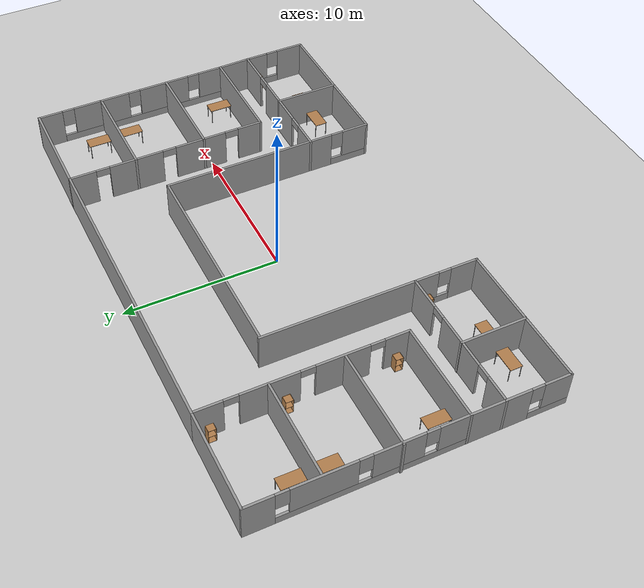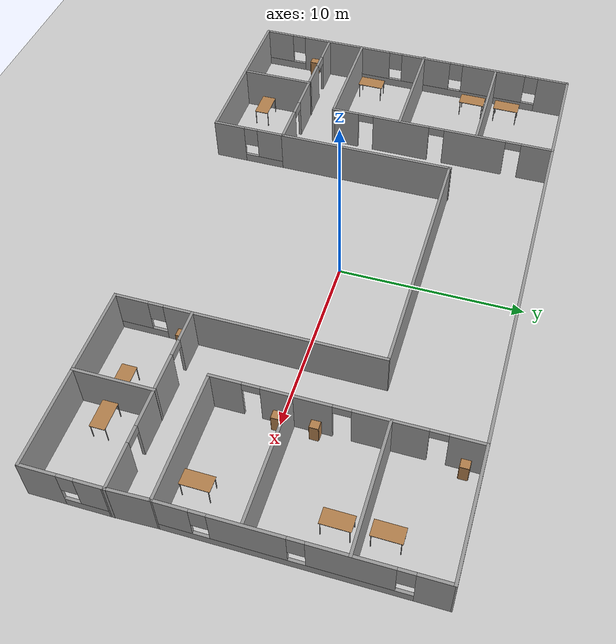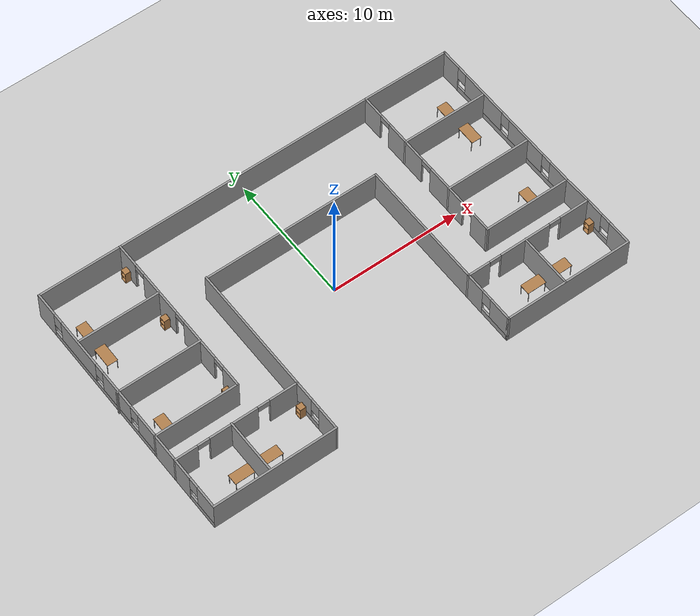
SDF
<sdf version="1.7">
 <world name="default">
  <light name="sun" type="directional">
   <pose>0 0 10 0 -0 0</pose>
   <diffuse>0.8 0.8 0.8 1</diffuse>
   <specular>0.2 0.2 0.2 1</specular>
   <attenuation>
    <range>1000</range>
    <constant>0.9</constant>
    <linear>0.01</linear>
    <quadratic>0.001</quadratic>
   </attenuation>
   <direction>-0.5 0.1 -0.9</direction>
   <spot><inner_angle>0</inner_angle><outer_angle>0</outer_angle><falloff>0</falloff></spot>
  </light>
  <model name="ground_plane">
   <static>1</static>
   <link name="link">
    <collision name="collision">
     <geometry><plane><normal>0 0 1</normal><size>100 100</size></plane></geometry>
     <surface><friction><ode><mu>100</mu><mu2>50</mu2></ode></friction></surface>
    </collision>
    <visual name="visual">
     <cast_shadows>0</cast_shadows>
     <geometry><plane><normal>0 0 1</normal><size>100 100</size></plane></geometry>
     <material>
      <script><uri>file://media/materials/scripts/gazebo.material</uri><name>Gazebo/Grey</name></script>
     </material>
    </visual>
   </link>
  </model>
  <gravity>0 0 -9.8</gravity>
  <magnetic_field>6e-06 2.3e-05 -4.2e-05</magnetic_field>
  <atmosphere type="adiabatic"/>
  <physics type="ode">
   <max_step_size>0.001</max_step_size>
   <real_time_factor>1</real_time_factor>
   <real_time_update_rate>1000</real_time_update_rate>
  </physics>
  <scene><ambient>0.4 0.4 0.4 1</ambient><background>0.7 0.7 0.7 1</background><shadows>1</shadows></scene>
  <audio><device>default</device></audio>
  <spherical_coordinates>
   <surface_model>EARTH_WGS84</surface_model>
   <latitude_deg>0</latitude_deg>
   <longitude_deg>0</longitude_deg>
   <elevation>0</elevation>
   <heading_deg>0</heading_deg>
  </spherical_coordinates>
  <model name="hostel">
   <pose>0.044 0.014209 0 0 -0 0</pose>
   <link name="Wall_1">
    <collision name="Wall_1_Collision">
     <geometry><box><size>10 0.15 2.5</size></box></geometry>
     <pose>0 0 1.25 0 -0 0</pose>
    </collision>
    <visual name="Wall_1_Visual">
     <pose>0 0 1.25 0 -0 0</pose>
     <geometry><box><size>10 0.15 2.5</size></box></geometry>
     <material>
      <script><uri>file://media/materials/scripts/gazebo.material</uri><name>Gazebo/Grey</name></script>
      <ambient>1 1 1 1</ambient>
     </material>
     <meta><layer>0</layer></meta>
    </visual>
    <pose>6.59221 -0.625321 0 0 -0 -1.5708</pose>
   </link>
   <link name="Wall_11">
    <collision name="Wall_11_Collision">
     <geometry><box><size>2.29691 0.15 2.5</size></box></geometry>
     <pose>0 0 1.25 0 -0 0</pose>
    </collision>
    <visual name="Wall_11_Visual">
     <pose>0 0 1.25 0 -0 0</pose>
     <geometry><box><size>2.29691 0.15 2.5</size></box></geometry>
     <material>
      <script><uri>file://media/materials/scripts/gazebo.material</uri><name>Gazebo/Grey</name></script>
      <ambient>1 1 1 1</ambient>
     </material>
     <meta><layer>0</layer></meta>
    </visual>
    <pose>-16.3577 -4.38382 0 0 -0 -1.57085</pose>
   </link>
   <link name="Wall_12">
    <pose>-11.6828 -5.45727 0 0 -0 0</pose>
    <visual name="Wall_12_Visual_0">
     <pose>-3.86628 0 1.25 0 -0 0</pose>
     <geometry><box><size>1.76744 0.15 2.5</size></box></geometry>
     <material>
      <script><uri>file://media/materials/scripts/gazebo.material</uri><name>Gazebo/Grey</name></script>
      <ambient>1 1 1 1</ambient>
     </material>
     <meta><layer>0</layer></meta>
    </visual>
    <collision name="Wall_12_Collision_0">
     <geometry><box><size>1.76744 0.15 2.5</size></box></geometry>
     <pose>-3.86628 0 1.25 0 -0 0</pose>
    </collision>
    <visual name="Wall_12_Visual_1">
     <pose>-0.229623 0 1.25 0 -0 0</pose>
     <geometry><box><size>3.70587 0.15 2.5</size></box></geometry>
     <material>
      <script><uri>file://media/materials/scripts/gazebo.material</uri><name>Gazebo/Grey</name></script>
      <ambient>1 1 1 1</ambient>
     </material>
     <meta><layer>0</layer></meta>
    </visual>
    <collision name="Wall_12_Collision_1">
     <geometry><box><size>3.70587 0.15 2.5</size></box></geometry>
     <pose>-0.229623 0 1.25 0 -0 0</pose>
    </collision>
    <visual name="Wall_12_Visual_2">
     <pose>3.63666 0 1.25 0 -0 0</pose>
     <geometry><box><size>2.22669 0.15 2.5</size></box></geometry>
     <material>
      <script><uri>file://media/materials/scripts/gazebo.material</uri><name>Gazebo/Grey</name></script>
      <ambient>1 1 1 1</ambient>
     </material>
     <meta><layer>0</layer></meta>
    </visual>
    <collision name="Wall_12_Collision_2">
     <geometry><box><size>2.22669 0.15 2.5</size></box></geometry>
     <pose>3.63666 0 1.25 0 -0 0</pose>
    </collision>
    <visual name="Wall_12_Visual_3">
     <pose>-2.53256 0 2.25 0 -0 0</pose>
     <geometry><box><size>0.9 0.15 0.5</size></box></geometry>
     <material>
      <script><uri>file://media/materials/scripts/gazebo.material</uri><name>Gazebo/Grey</name></script>
      <ambient>1 1 1 1</ambient>
     </material>
     <meta><layer>0</layer></meta>
    </visual>
    <collision name="Wall_12_Collision_3">
     <geometry><box><size>0.9 0.15 0.5</size></box></geometry>
     <pose>-2.53256 0 2.25 0 -0 0</pose>
    </collision>
    <visual name="Wall_12_Visual_4">
     <pose>2.07331 0 2.25 0 -0 0</pose>
     <geometry><box><size>0.9 0.15 0.5</size></box></geometry>
     <material>
      <script><uri>file://media/materials/scripts/gazebo.material</uri><name>Gazebo/Grey</name></script>
      <ambient>1 1 1 1</ambient>
     </material>
     <meta><layer>0</layer></meta>
    </visual>
    <collision name="Wall_12_Collision_4">
     <geometry><box><size>0.9 0.15 0.5</size></box></geometry>
     <pose>2.07331 0 2.25 0 -0 0</pose>
    </collision>
   </link>
   <link name="Wall_13">
    <collision name="Wall_13_Collision">
     <geometry><box><size>9.98262 0.15 2.5</size></box></geometry>
     <pose>0 0 1.25 0 -0 0</pose>
    </collision>
    <visual name="Wall_13_Visual">
     <pose>0 0 1.25 0 -0 0</pose>
     <geometry><box><size>9.98262 0.15 2.5</size></box></geometry>
     <material>
      <script><uri>file://media/materials/scripts/gazebo.material</uri><name>Gazebo/Grey</name></script>
      <ambient>1 1 1 1</ambient>
     </material>
     <meta><layer>0</layer></meta>
    </visual>
    <pose>-7.00779 -0.540964 0 0 -0 1.5708</pose>
   </link>
   <link name="Wall_14">
    <collision name="Wall_14_Collision">
     <geometry><box><size>13.75 0.15 2.5</size></box></geometry>
     <pose>0 0 1.25 0 -0 0</pose>
    </collision>
    <visual name="Wall_14_Visual">
     <pose>0 0 1.25 0 -0 0</pose>
     <geometry><box><size>13.75 0.15 2.5</size></box></geometry>
     <material>
      <script><uri>file://media/materials/scripts/gazebo.material</uri><name>Gazebo/Grey</name></script>
      <ambient>1 1 1 1</ambient>
     </material>
     <meta><layer>0</layer></meta>
    </visual>
    <pose>-0.207788 4.32882 0 0 -0 0</pose>
   </link>
   <link name="Wall_16">
    <pose>6.59221 -7.60032 0 0 -0 -1.5708</pose>
    <visual name="Wall_16_Visual_0">
     <pose>-1.32614 0 1.25 0 -0 0</pose>
     <geometry><box><size>1.59771 0.15 2.5</size></box></geometry>
     <material>
      <script><uri>file://media/materials/scripts/gazebo.material</uri><name>Gazebo/Grey</name></script>
      <ambient>1 1 1 1</ambient>
     </material>
     <meta><layer>0</layer></meta>
    </visual>
    <collision name="Wall_16_Collision_0">
     <geometry><box><size>1.59771 0.15 2.5</size></box></geometry>
     <pose>-1.32614 0 1.25 0 -0 0</pose>
    </collision>
    <visual name="Wall_16_Visual_1">
     <pose>0.798857 0 0.25 0 -0 0</pose>
     <geometry><box><size>2.65229 0.15 0.5</size></box></geometry>
     <material>
      <script><uri>file://media/materials/scripts/gazebo.material</uri><name>Gazebo/Grey</name></script>
      <ambient>1 1 1 1</ambient>
     </material>
     <meta><layer>0</layer></meta>
    </visual>
    <collision name="Wall_16_Collision_1">
     <geometry><box><size>2.65229 0.15 0.5</size></box></geometry>
     <pose>0.798857 0 0.25 0 -0 0</pose>
    </collision>
    <visual name="Wall_16_Visual_2">
     <pose>1.19886 0 1.5 0 -0 0</pose>
     <geometry><box><size>1.85229 0.15 2</size></box></geometry>
     <material>
      <script><uri>file://media/materials/scripts/gazebo.material</uri><name>Gazebo/Grey</name></script>
      <ambient>1 1 1 1</ambient>
     </material>
     <meta><layer>0</layer></meta>
    </visual>
    <collision name="Wall_16_Collision_2">
     <geometry><box><size>1.85229 0.15 2</size></box></geometry>
     <pose>1.19886 0 1.5 0 -0 0</pose>
    </collision>
    <visual name="Wall_16_Visual_3">
     <pose>-0.127286 0 1.9 0 -0 0</pose>
     <geometry><box><size>0.8 0.15 1.2</size></box></geometry>
     <material>
      <script><uri>file://media/materials/scripts/gazebo.material</uri><name>Gazebo/Grey</name></script>
      <ambient>1 1 1 1</ambient>
     </material>
     <meta><layer>0</layer></meta>
    </visual>
    <collision name="Wall_16_Collision_3">
     <geometry><box><size>0.8 0.15 1.2</size></box></geometry>
     <pose>-0.127286 0 1.9 0 -0 0</pose>
    </collision>
   </link>
   <link name="Wall_17">
    <collision name="Wall_17_Collision">
     <geometry><box><size>10 0.15 2.5</size></box></geometry>
     <pose>0 0 1.25 0 -0 0</pose>
    </collision>
    <visual name="Wall_17_Visual">
     <pose>0 0 1.25 0 -0 0</pose>
     <geometry><box><size>10 0.15 2.5</size></box></geometry>
     <material>
      <script><uri>file://media/materials/scripts/gazebo.material</uri><name>Gazebo/Grey</name></script>
      <ambient>1 1 1 1</ambient>
     </material>
     <meta><layer>0</layer></meta>
    </visual>
    <pose>11.5172 -9.65032 0 0 -0 0</pose>
   </link>
   <link name="Wall_18">
    <pose>16.4422 -7.60032 0 0 -0 1.5708</pose>
    <visual name="Wall_18_Visual_0">
     <pose>-1.16809 0 1.25 0 -0 0</pose>
     <geometry><box><size>1.91381 0.15 2.5</size></box></geometry>
     <material>
      <script><uri>file://media/materials/scripts/gazebo.material</uri><name>Gazebo/Grey</name></script>
      <ambient>1 1 1 1</ambient>
     </material>
     <meta><layer>0</layer></meta>
    </visual>
    <collision name="Wall_18_Collision_0">
     <geometry><box><size>1.91381 0.15 2.5</size></box></geometry>
     <pose>-1.16809 0 1.25 0 -0 0</pose>
    </collision>
    <visual name="Wall_18_Visual_1">
     <pose>0.956907 0 0.25 0 -0 0</pose>
     <geometry><box><size>2.33619 0.15 0.5</size></box></geometry>
     <material>
      <script><uri>file://media/materials/scripts/gazebo.material</uri><name>Gazebo/Grey</name></script>
      <ambient>1 1 1 1</ambient>
     </material>
     <meta><layer>0</layer></meta>
    </visual>
    <collision name="Wall_18_Collision_1">
     <geometry><box><size>2.33619 0.15 0.5</size></box></geometry>
     <pose>0.956907 0 0.25 0 -0 0</pose>
    </collision>
    <visual name="Wall_18_Visual_2">
     <pose>1.35691 0 1.5 0 -0 0</pose>
     <geometry><box><size>1.53619 0.15 2</size></box></geometry>
     <material>
      <script><uri>file://media/materials/scripts/gazebo.material</uri><name>Gazebo/Grey</name></script>
      <ambient>1 1 1 1</ambient>
     </material>
     <meta><layer>0</layer></meta>
    </visual>
    <collision name="Wall_18_Collision_2">
     <geometry><box><size>1.53619 0.15 2</size></box></geometry>
     <pose>1.35691 0 1.5 0 -0 0</pose>
    </collision>
    <visual name="Wall_18_Visual_3">
     <pose>0.188814 0 1.9 0 -0 0</pose>
     <geometry><box><size>0.8 0.15 1.2</size></box></geometry>
     <material>
      <script><uri>file://media/materials/scripts/gazebo.material</uri><name>Gazebo/Grey</name></script>
      <ambient>1 1 1 1</ambient>
     </material>
     <meta><layer>0</layer></meta>
    </visual>
    <collision name="Wall_18_Collision_3">
     <geometry><box><size>0.8 0.15 1.2</size></box></geometry>
     <pose>0.188814 0 1.9 0 -0 0</pose>
    </collision>
   </link>
   <link name="Wall_2">
    <pose>11.5172 -5.55032 0 0 -0 0</pose>
    <visual name="Wall_2_Visual_0">
     <pose>-4.10829 0 1.25 0 -0 0</pose>
     <geometry><box><size>1.78361 0.15 2.5</size></box></geometry>
     <material>
      <script><uri>file://media/materials/scripts/gazebo.material</uri><name>Gazebo/Grey</name></script>
      <ambient>1 1 1 1</ambient>
     </material>
     <meta><layer>0</layer></meta>
    </visual>
    <collision name="Wall_2_Collision_0">
     <geometry><box><size>1.78361 0.15 2.5</size></box></geometry>
     <pose>-4.10829 0 1.25 0 -0 0</pose>
    </collision>
    <visual name="Wall_2_Visual_1">
     <pose>-0.303969 0 1.25 0 -0 0</pose>
     <geometry><box><size>4.02503 0.15 2.5</size></box></geometry>
     <material>
      <script><uri>file://media/materials/scripts/gazebo.material</uri><name>Gazebo/Grey</name></script>
      <ambient>1 1 1 1</ambient>
     </material>
     <meta><layer>0</layer></meta>
    </visual>
    <collision name="Wall_2_Collision_1">
     <geometry><box><size>4.02503 0.15 2.5</size></box></geometry>
     <pose>-0.303969 0 1.25 0 -0 0</pose>
    </collision>
    <visual name="Wall_2_Visual_2">
     <pose>3.80432 0 1.25 0 -0 0</pose>
     <geometry><box><size>2.39155 0.15 2.5</size></box></geometry>
     <material>
      <script><uri>file://media/materials/scripts/gazebo.material</uri><name>Gazebo/Grey</name></script>
      <ambient>1 1 1 1</ambient>
     </material>
     <meta><layer>0</layer></meta>
    </visual>
    <collision name="Wall_2_Collision_2">
     <geometry><box><size>2.39155 0.15 2.5</size></box></geometry>
     <pose>3.80432 0 1.25 0 -0 0</pose>
    </collision>
    <visual name="Wall_2_Visual_3">
     <pose>-2.76648 0 2.25 0 -0 0</pose>
     <geometry><box><size>0.9 0.15 0.5</size></box></geometry>
     <material>
      <script><uri>file://media/materials/scripts/gazebo.material</uri><name>Gazebo/Grey</name></script>
      <ambient>1 1 1 1</ambient>
     </material>
     <meta><layer>0</layer></meta>
    </visual>
    <collision name="Wall_2_Collision_3">
     <geometry><box><size>0.9 0.15 0.5</size></box></geometry>
     <pose>-2.76648 0 2.25 0 -0 0</pose>
    </collision>
    <visual name="Wall_2_Visual_4">
     <pose>2.15855 0 2.25 0 -0 0</pose>
     <geometry><box><size>0.9 0.15 0.5</size></box></geometry>
     <material>
      <script><uri>file://media/materials/scripts/gazebo.material</uri><name>Gazebo/Grey</name></script>
      <ambient>1 1 1 1</ambient>
     </material>
     <meta><layer>0</layer></meta>
    </visual>
    <collision name="Wall_2_Collision_4">
     <geometry><box><size>0.9 0.15 0.5</size></box></geometry>
     <pose>2.15855 0 2.25 0 -0 0</pose>
    </collision>
   </link>
   <link name="Wall_20">
    <collision name="Wall_20_Collision">
     <geometry><box><size>4.25 0.15 2.5</size></box></geometry>
     <pose>0 0 1.25 0 -0 0</pose>
    </collision>
    <visual name="Wall_20_Visual">
     <pose>0 0 1.25 0 -0 0</pose>
     <geometry><box><size>4.25 0.15 2.5</size></box></geometry>
     <material>
      <script><uri>file://media/materials/scripts/gazebo.material</uri><name>Gazebo/Grey</name></script>
      <ambient>1 1 1 1</ambient>
     </material>
     <meta><layer>0</layer></meta>
    </visual>
    <pose>11.2484 -7.58527 0 0 -0 -1.5708</pose>
   </link>
   <link name="Wall_22">
    <pose>-16.3578 -7.50727 0 0 -0 -1.5708</pose>
    <visual name="Wall_22_Visual_0">
     <pose>-1.27962 0 1.25 0 -0 0</pose>
     <geometry><box><size>1.69076 0.15 2.5</size></box></geometry>
     <material>
      <script><uri>file://media/materials/scripts/gazebo.material</uri><name>Gazebo/Grey</name></script>
      <ambient>1 1 1 1</ambient>
     </material>
     <meta><layer>0</layer></meta>
    </visual>
    <collision name="Wall_22_Collision_0">
     <geometry><box><size>1.69076 0.15 2.5</size></box></geometry>
     <pose>-1.27962 0 1.25 0 -0 0</pose>
    </collision>
    <visual name="Wall_22_Visual_1">
     <pose>0.845381 0 0.25 0 -0 0</pose>
     <geometry><box><size>2.55924 0.15 0.5</size></box></geometry>
     <material>
      <script><uri>file://media/materials/scripts/gazebo.material</uri><name>Gazebo/Grey</name></script>
      <ambient>1 1 1 1</ambient>
     </material>
     <meta><layer>0</layer></meta>
    </visual>
    <collision name="Wall_22_Collision_1">
     <geometry><box><size>2.55924 0.15 0.5</size></box></geometry>
     <pose>0.845381 0 0.25 0 -0 0</pose>
    </collision>
    <visual name="Wall_22_Visual_2">
     <pose>1.24538 0 1.5 0 -0 0</pose>
     <geometry><box><size>1.75924 0.15 2</size></box></geometry>
     <material>
      <script><uri>file://media/materials/scripts/gazebo.material</uri><name>Gazebo/Grey</name></script>
      <ambient>1 1 1 1</ambient>
     </material>
     <meta><layer>0</layer></meta>
    </visual>
    <collision name="Wall_22_Collision_2">
     <geometry><box><size>1.75924 0.15 2</size></box></geometry>
     <pose>1.24538 0 1.5 0 -0 0</pose>
    </collision>
    <visual name="Wall_22_Visual_3">
     <pose>-0.034238 0 1.9 0 -0 0</pose>
     <geometry><box><size>0.8 0.15 1.2</size></box></geometry>
     <material>
      <script><uri>file://media/materials/scripts/gazebo.material</uri><name>Gazebo/Grey</name></script>
      <ambient>1 1 1 1</ambient>
     </material>
     <meta><layer>0</layer></meta>
    </visual>
    <collision name="Wall_22_Collision_3">
     <geometry><box><size>0.8 0.15 1.2</size></box></geometry>
     <pose>-0.034238 0 1.9 0 -0 0</pose>
    </collision>
   </link>
   <link name="Wall_23">
    <collision name="Wall_23_Collision">
     <geometry><box><size>9.5 0.15 2.5</size></box></geometry>
     <pose>0 0 1.25 0 -0 0</pose>
    </collision>
    <visual name="Wall_23_Visual">
     <pose>0 0 1.25 0 -0 0</pose>
     <geometry><box><size>9.5 0.15 2.5</size></box></geometry>
     <material>
      <script><uri>file://media/materials/scripts/gazebo.material</uri><name>Gazebo/Grey</name></script>
      <ambient>1 1 1 1</ambient>
     </material>
     <meta><layer>0</layer></meta>
    </visual>
    <pose>-11.6828 -9.55727 0 0 -0 0</pose>
   </link>
   <link name="Wall_24">
    <pose>-7.00779 -7.50727 0 0 -0 1.5708</pose>
    <visual name="Wall_24_Visual_0">
     <pose>-1.21462 0 1.25 0 -0 0</pose>
     <geometry><box><size>1.82077 0.15 2.5</size></box></geometry>
     <material>
      <script><uri>file://media/materials/scripts/gazebo.material</uri><name>Gazebo/Grey</name></script>
      <ambient>1 1 1 1</ambient>
     </material>
     <meta><layer>0</layer></meta>
    </visual>
    <collision name="Wall_24_Collision_0">
     <geometry><box><size>1.82077 0.15 2.5</size></box></geometry>
     <pose>-1.21462 0 1.25 0 -0 0</pose>
    </collision>
    <visual name="Wall_24_Visual_1">
     <pose>0.910383 0 0.25 0 -0 0</pose>
     <geometry><box><size>2.42923 0.15 0.5</size></box></geometry>
     <material>
      <script><uri>file://media/materials/scripts/gazebo.material</uri><name>Gazebo/Grey</name></script>
      <ambient>1 1 1 1</ambient>
     </material>
     <meta><layer>0</layer></meta>
    </visual>
    <collision name="Wall_24_Collision_1">
     <geometry><box><size>2.42923 0.15 0.5</size></box></geometry>
     <pose>0.910383 0 0.25 0 -0 0</pose>
    </collision>
    <visual name="Wall_24_Visual_2">
     <pose>1.31038 0 1.5 0 -0 0</pose>
     <geometry><box><size>1.62923 0.15 2</size></box></geometry>
     <material>
      <script><uri>file://media/materials/scripts/gazebo.material</uri><name>Gazebo/Grey</name></script>
      <ambient>1 1 1 1</ambient>
     </material>
     <meta><layer>0</layer></meta>
    </visual>
    <collision name="Wall_24_Collision_2">
     <geometry><box><size>1.62923 0.15 2</size></box></geometry>
     <pose>1.31038 0 1.5 0 -0 0</pose>
    </collision>
    <visual name="Wall_24_Visual_3">
     <pose>0.095766 0 1.9 0 -0 0</pose>
     <geometry><box><size>0.8 0.15 1.2</size></box></geometry>
     <material>
      <script><uri>file://media/materials/scripts/gazebo.material</uri><name>Gazebo/Grey</name></script>
      <ambient>1 1 1 1</ambient>
     </material>
     <meta><layer>0</layer></meta>
    </visual>
    <collision name="Wall_24_Collision_3">
     <geometry><box><size>0.8 0.15 1.2</size></box></geometry>
     <pose>0.095766 0 1.9 0 -0 0</pose>
    </collision>
   </link>
   <link name="Wall_26">
    <collision name="Wall_26_Collision">
     <geometry><box><size>4.25 0.15 2.5</size></box></geometry>
     <pose>0 0 1.25 0 -0 0</pose>
    </collision>
    <visual name="Wall_26_Visual">
     <pose>0 0 1.25 0 -0 0</pose>
     <geometry><box><size>4.25 0.15 2.5</size></box></geometry>
     <material>
      <script><uri>file://media/materials/scripts/gazebo.material</uri><name>Gazebo/Grey</name></script>
      <ambient>1 1 1 1</ambient>
     </material>
     <meta><layer>0</layer></meta>
    </visual>
    <pose>-12.0389 -7.47388 0 0 -0 -1.5708</pose>
   </link>
   <link name="Wall_28">
    <collision name="Wall_28_Collision">
     <geometry><box><size>6.75028 0.15 2.5</size></box></geometry>
     <pose>0 0 1.25 0 -0 0</pose>
    </collision>
    <visual name="Wall_28_Visual">
     <pose>0 0 1.25 0 -0 0</pose>
     <geometry><box><size>6.75028 0.15 2.5</size></box></geometry>
     <material>
      <script><uri>file://media/materials/scripts/gazebo.material</uri><name>Gazebo/Grey</name></script>
      <ambient>1 1 1 1</ambient>
     </material>
     <meta><layer>0</layer></meta>
    </visual>
    <pose>13.0803 9.61913 0 0 -0 -0.009242</pose>
   </link>
   <link name="Wall_29">
    <pose>16.3803 3.07113 0 0 -0 -1.5708</pose>
    <visual name="Wall_29_Visual_0">
     <pose>-5.76136 0 1.25 0 -0 0</pose>
     <geometry><box><size>1.66239 0.15 2.5</size></box></geometry>
     <material>
      <script><uri>file://media/materials/scripts/gazebo.material</uri><name>Gazebo/Grey</name></script>
      <ambient>1 1 1 1</ambient>
     </material>
     <meta><layer>0</layer></meta>
    </visual>
    <collision name="Wall_29_Collision_0">
     <geometry><box><size>1.66239 0.15 2.5</size></box></geometry>
     <pose>-5.76136 0 1.25 0 -0 0</pose>
    </collision>
    <visual name="Wall_29_Visual_1">
     <pose>0.831193 0 0.25 0 -0 0</pose>
     <geometry><box><size>11.5227 0.15 0.5</size></box></geometry>
     <material>
      <script><uri>file://media/materials/scripts/gazebo.material</uri><name>Gazebo/Grey</name></script>
      <ambient>1 1 1 1</ambient>
     </material>
     <meta><layer>0</layer></meta>
    </visual>
    <collision name="Wall_29_Collision_1">
     <geometry><box><size>11.5227 0.15 0.5</size></box></geometry>
     <pose>0.831193 0 0.25 0 -0 0</pose>
    </collision>
    <visual name="Wall_29_Visual_2">
     <pose>-2.1921 0 1.5 0 -0 0</pose>
     <geometry><box><size>3.87612 0.15 2</size></box></geometry>
     <material>
      <script><uri>file://media/materials/scripts/gazebo.material</uri><name>Gazebo/Grey</name></script>
      <ambient>1 1 1 1</ambient>
     </material>
     <meta><layer>0</layer></meta>
    </visual>
    <collision name="Wall_29_Collision_2">
     <geometry><box><size>3.87612 0.15 2</size></box></geometry>
     <pose>-2.1921 0 1.5 0 -0 0</pose>
    </collision>
    <visual name="Wall_29_Visual_3">
     <pose>2.29943 0 1.5 0 -0 0</pose>
     <geometry><box><size>3.50695 0.15 2</size></box></geometry>
     <material>
      <script><uri>file://media/materials/scripts/gazebo.material</uri><name>Gazebo/Grey</name></script>
      <ambient>1 1 1 1</ambient>
     </material>
     <meta><layer>0</layer></meta>
    </visual>
    <collision name="Wall_29_Collision_3">
     <geometry><box><size>3.50695 0.15 2</size></box></geometry>
     <pose>2.29943 0 1.5 0 -0 0</pose>
    </collision>
    <visual name="Wall_29_Visual_4">
     <pose>5.72273 0 1.5 0 -0 0</pose>
     <geometry><box><size>1.73964 0.15 2</size></box></geometry>
     <material>
      <script><uri>file://media/materials/scripts/gazebo.material</uri><name>Gazebo/Grey</name></script>
      <ambient>1 1 1 1</ambient>
     </material>
     <meta><layer>0</layer></meta>
    </visual>
    <collision name="Wall_29_Collision_4">
     <geometry><box><size>1.73964 0.15 2</size></box></geometry>
     <pose>5.72273 0 1.5 0 -0 0</pose>
    </collision>
    <visual name="Wall_29_Visual_5">
     <pose>-4.53016 0 1.9 0 -0 0</pose>
     <geometry><box><size>0.8 0.15 1.2</size></box></geometry>
     <material>
      <script><uri>file://media/materials/scripts/gazebo.material</uri><name>Gazebo/Grey</name></script>
      <ambient>1 1 1 1</ambient>
     </material>
     <meta><layer>0</layer></meta>
    </visual>
    <collision name="Wall_29_Collision_5">
     <geometry><box><size>0.8 0.15 1.2</size></box></geometry>
     <pose>-4.53016 0 1.9 0 -0 0</pose>
    </collision>
    <visual name="Wall_29_Visual_6">
     <pose>0.145957 0 1.9 0 -0 0</pose>
     <geometry><box><size>0.8 0.15 1.2</size></box></geometry>
     <material>
      <script><uri>file://media/materials/scripts/gazebo.material</uri><name>Gazebo/Grey</name></script>
      <ambient>1 1 1 1</ambient>
     </material>
     <meta><layer>0</layer></meta>
    </visual>
    <collision name="Wall_29_Collision_6">
     <geometry><box><size>0.8 0.15 1.2</size></box></geometry>
     <pose>0.145957 0 1.9 0 -0 0</pose>
    </collision>
    <visual name="Wall_29_Visual_7">
     <pose>4.45291 0 1.9 0 -0 0</pose>
     <geometry><box><size>0.8 0.15 1.2</size></box></geometry>
     <material>
      <script><uri>file://media/materials/scripts/gazebo.material</uri><name>Gazebo/Grey</name></script>
      <ambient>1 1 1 1</ambient>
     </material>
     <meta><layer>0</layer></meta>
    </visual>
    <collision name="Wall_29_Collision_7">
     <geometry><box><size>0.8 0.15 1.2</size></box></geometry>
     <pose>4.45291 0 1.9 0 -0 0</pose>
    </collision>
   </link>
   <link name="Wall_3">
    <collision name="Wall_3_Collision">
     <geometry><box><size>2.31629 0.15 2.5</size></box></geometry>
     <pose>0 0 1.25 0 -0 0</pose>
    </collision>
    <visual name="Wall_3_Visual">
     <pose>0 0 1.25 0 -0 0</pose>
     <geometry><box><size>2.31629 0.15 2.5</size></box></geometry>
     <material>
      <script><uri>file://media/materials/scripts/gazebo.material</uri><name>Gazebo/Grey</name></script>
      <ambient>1 1 1 1</ambient>
     </material>
     <meta><layer>0</layer></meta>
    </visual>
    <pose>16.4113 -4.52911 0 0 -0 1.59936</pose>
   </link>
   <link name="Wall_31">
    <collision name="Wall_31_Collision">
     <geometry><box><size>6.37306 0.15 2.5</size></box></geometry>
     <pose>0 0 1.25 0 -0 0</pose>
    </collision>
    <visual name="Wall_31_Visual">
     <pose>0 0 1.25 0 -0 0</pose>
     <geometry><box><size>6.37306 0.15 2.5</size></box></geometry>
     <material>
      <script><uri>file://media/materials/scripts/gazebo.material</uri><name>Gazebo/Grey</name></script>
      <ambient>1 1 1 1</ambient>
     </material>
     <meta><layer>0</layer></meta>
    </visual>
    <pose>-13.181 9.64965 0 0 -0 3.14159</pose>
   </link>
   <link name="Wall_32">
    <pose>-16.3539 3.22468 0 0 -0 -1.5708</pose>
    <visual name="Wall_32_Visual_0">
     <pose>-5.57678 0 1.25 0 -0 0</pose>
     <geometry><box><size>1.84644 0.15 2.5</size></box></geometry>
     <material>
      <script><uri>file://media/materials/scripts/gazebo.material</uri><name>Gazebo/Grey</name></script>
      <ambient>1 1 1 1</ambient>
     </material>
     <meta><layer>0</layer></meta>
    </visual>
    <collision name="Wall_32_Collision_0">
     <geometry><box><size>1.84644 0.15 2.5</size></box></geometry>
     <pose>-5.57678 0 1.25 0 -0 0</pose>
    </collision>
    <visual name="Wall_32_Visual_1">
     <pose>0.92322 0 0.25 0 -0 0</pose>
     <geometry><box><size>11.1536 0.15 0.5</size></box></geometry>
     <material>
      <script><uri>file://media/materials/scripts/gazebo.material</uri><name>Gazebo/Grey</name></script>
      <ambient>1 1 1 1</ambient>
     </material>
     <meta><layer>0</layer></meta>
    </visual>
    <collision name="Wall_32_Collision_1">
     <geometry><box><size>11.1536 0.15 0.5</size></box></geometry>
     <pose>0.92322 0 0.25 0 -0 0</pose>
    </collision>
    <visual name="Wall_32_Visual_2">
     <pose>-1.9155 0 1.5 0 -0 0</pose>
     <geometry><box><size>3.87612 0.15 2</size></box></geometry>
     <material>
      <script><uri>file://media/materials/scripts/gazebo.material</uri><name>Gazebo/Grey</name></script>
      <ambient>1 1 1 1</ambient>
     </material>
     <meta><layer>0</layer></meta>
    </visual>
    <collision name="Wall_32_Collision_2">
     <geometry><box><size>3.87612 0.15 2</size></box></geometry>
     <pose>-1.9155 0 1.5 0 -0 0</pose>
    </collision>
    <visual name="Wall_32_Visual_3">
     <pose>2.36069 0 1.5 0 -0 0</pose>
     <geometry><box><size>3.07626 0.15 2</size></box></geometry>
     <material>
      <script><uri>file://media/materials/scripts/gazebo.material</uri><name>Gazebo/Grey</name></script>
      <ambient>1 1 1 1</ambient>
     </material>
     <meta><layer>0</layer></meta>
    </visual>
    <collision name="Wall_32_Collision_3">
     <geometry><box><size>3.07626 0.15 2</size></box></geometry>
     <pose>2.36069 0 1.5 0 -0 0</pose>
    </collision>
    <visual name="Wall_32_Visual_4">
     <pose>5.59941 0 1.5 0 -0 0</pose>
     <geometry><box><size>1.80119 0.15 2</size></box></geometry>
     <material>
      <script><uri>file://media/materials/scripts/gazebo.material</uri><name>Gazebo/Grey</name></script>
      <ambient>1 1 1 1</ambient>
     </material>
     <meta><layer>0</layer></meta>
    </visual>
    <collision name="Wall_32_Collision_4">
     <geometry><box><size>1.80119 0.15 2</size></box></geometry>
     <pose>5.59941 0 1.5 0 -0 0</pose>
    </collision>
    <visual name="Wall_32_Visual_5">
     <pose>-4.25356 0 1.9 0 -0 0</pose>
     <geometry><box><size>0.8 0.15 1.2</size></box></geometry>
     <material>
      <script><uri>file://media/materials/scripts/gazebo.material</uri><name>Gazebo/Grey</name></script>
      <ambient>1 1 1 1</ambient>
     </material>
     <meta><layer>0</layer></meta>
    </visual>
    <collision name="Wall_32_Collision_5">
     <geometry><box><size>0.8 0.15 1.2</size></box></geometry>
     <pose>-4.25356 0 1.9 0 -0 0</pose>
    </collision>
    <visual name="Wall_32_Visual_6">
     <pose>0.422558 0 1.9 0 -0 0</pose>
     <geometry><box><size>0.8 0.15 1.2</size></box></geometry>
     <material>
      <script><uri>file://media/materials/scripts/gazebo.material</uri><name>Gazebo/Grey</name></script>
      <ambient>1 1 1 1</ambient>
     </material>
     <meta><layer>0</layer></meta>
    </visual>
    <collision name="Wall_32_Collision_6">
     <geometry><box><size>0.8 0.15 1.2</size></box></geometry>
     <pose>0.422558 0 1.9 0 -0 0</pose>
    </collision>
    <visual name="Wall_32_Visual_7">
     <pose>4.29882 0 1.9 0 -0 0</pose>
     <geometry><box><size>0.8 0.15 1.2</size></box></geometry>
     <material>
      <script><uri>file://media/materials/scripts/gazebo.material</uri><name>Gazebo/Grey</name></script>
      <ambient>1 1 1 1</ambient>
     </material>
     <meta><layer>0</layer></meta>
    </visual>
    <collision name="Wall_32_Collision_7">
     <geometry><box><size>0.8 0.15 1.2</size></box></geometry>
     <pose>4.29882 0 1.9 0 -0 0</pose>
    </collision>
   </link>
   <link name="Wall_34">
    <collision name="Wall_34_Collision">
     <geometry><box><size>6.75 0.15 2.5</size></box></geometry>
     <pose>0 0 1.25 0 -0 0</pose>
    </collision>
    <visual name="Wall_34_Visual">
     <pose>0 0 1.25 0 -0 0</pose>
     <geometry><box><size>6.75 0.15 2.5</size></box></geometry>
     <material>
      <script><uri>file://media/materials/scripts/gazebo.material</uri><name>Gazebo/Grey</name></script>
      <ambient>1 1 1 1</ambient>
     </material>
     <meta><layer>0</layer></meta>
    </visual>
    <pose>13.0792 0.587116 0 0 -0 0</pose>
   </link>
   <link name="Wall_36">
    <collision name="Wall_36_Collision">
     <geometry><box><size>6.75 0.15 2.5</size></box></geometry>
     <pose>0 0 1.25 0 -0 0</pose>
    </collision>
    <visual name="Wall_36_Visual">
     <pose>0 0 1.25 0 -0 0</pose>
     <geometry><box><size>6.75 0.15 2.5</size></box></geometry>
     <material>
      <script><uri>file://media/materials/scripts/gazebo.material</uri><name>Gazebo/Grey</name></script>
      <ambient>1 1 1 1</ambient>
     </material>
     <meta><layer>0</layer></meta>
    </visual>
    <pose>13.0792 5.26323 0 0 -0 0</pose>
   </link>
   <link name="Wall_38">
    <collision name="Wall_38_Collision">
     <geometry><box><size>6.5 0.15 2.5</size></box></geometry>
     <pose>0 0 1.25 0 -0 0</pose>
    </collision>
    <visual name="Wall_38_Visual">
     <pose>0 0 1.25 0 -0 0</pose>
     <geometry><box><size>6.5 0.15 2.5</size></box></geometry>
     <material>
      <script><uri>file://media/materials/scripts/gazebo.material</uri><name>Gazebo/Grey</name></script>
      <ambient>1 1 1 1</ambient>
     </material>
     <meta><layer>0</layer></meta>
    </visual>
    <pose>-13.2693 0.710172 0 0 -0 3.14159</pose>
   </link>
   <link name="Wall_4">
    <collision name="Wall_4_Collision">
     <geometry><box><size>6.75 0.15 2.5</size></box></geometry>
     <pose>0 0 1.25 0 -0 0</pose>
    </collision>
    <visual name="Wall_4_Visual">
     <pose>0 0 1.25 0 -0 0</pose>
     <geometry><box><size>6.75 0.15 2.5</size></box></geometry>
     <material>
      <script><uri>file://media/materials/scripts/gazebo.material</uri><name>Gazebo/Grey</name></script>
      <ambient>1 1 1 1</ambient>
     </material>
     <meta><layer>0</layer></meta>
    </visual>
    <pose>13.0803 -3.44637 0 0 -0 3.14159</pose>
   </link>
   <link name="Wall_40">
    <collision name="Wall_40_Collision">
     <geometry><box><size>6.25 0.15 2.5</size></box></geometry>
     <pose>0 0 1.25 0 -0 0</pose>
    </collision>
    <visual name="Wall_40_Visual">
     <pose>0 0 1.25 0 -0 0</pose>
     <geometry><box><size>6.25 0.15 2.5</size></box></geometry>
     <material>
      <script><uri>file://media/materials/scripts/gazebo.material</uri><name>Gazebo/Grey</name></script>
      <ambient>1 1 1 1</ambient>
     </material>
     <meta><layer>0</layer></meta>
    </visual>
    <pose>-13.2059 5.26323 0 0 -0 3.14159</pose>
   </link>
   <link name="Wall_5">
    <pose>9.78033 3.10163 0 0 -0 1.5708</pose>
    <visual name="Wall_5_Visual_0">
     <pose>-5.77836 0 1.25 0 -0 0</pose>
     <geometry><box><size>1.6899 0.15 2.5</size></box></geometry>
     <material>
      <script><uri>file://media/materials/scripts/gazebo.material</uri><name>Gazebo/Grey</name></script>
      <ambient>1 1 1 1</ambient>
     </material>
     <meta><layer>0</layer></meta>
    </visual>
    <collision name="Wall_5_Collision_0">
     <geometry><box><size>1.6899 0.15 2.5</size></box></geometry>
     <pose>-5.77836 0 1.25 0 -0 0</pose>
    </collision>
    <visual name="Wall_5_Visual_1">
     <pose>-2.29917 0 1.25 0 -0 0</pose>
     <geometry><box><size>3.46848 0.15 2.5</size></box></geometry>
     <material>
      <script><uri>file://media/materials/scripts/gazebo.material</uri><name>Gazebo/Grey</name></script>
      <ambient>1 1 1 1</ambient>
     </material>
     <meta><layer>0</layer></meta>
    </visual>
    <collision name="Wall_5_Collision_1">
     <geometry><box><size>3.46848 0.15 2.5</size></box></geometry>
     <pose>-2.29917 0 1.25 0 -0 0</pose>
    </collision>
    <visual name="Wall_5_Visual_2">
     <pose>2.13084 0 1.25 0 -0 0</pose>
     <geometry><box><size>3.59153 0.15 2.5</size></box></geometry>
     <material>
      <script><uri>file://media/materials/scripts/gazebo.material</uri><name>Gazebo/Grey</name></script>
      <ambient>1 1 1 1</ambient>
     </material>
     <meta><layer>0</layer></meta>
    </visual>
    <collision name="Wall_5_Collision_2">
     <geometry><box><size>3.59153 0.15 2.5</size></box></geometry>
     <pose>2.13084 0 1.25 0 -0 0</pose>
    </collision>
    <visual name="Wall_5_Visual_3">
     <pose>5.72496 0 1.25 0 -0 0</pose>
     <geometry><box><size>1.7967 0.15 2.5</size></box></geometry>
     <material>
      <script><uri>file://media/materials/scripts/gazebo.material</uri><name>Gazebo/Grey</name></script>
      <ambient>1 1 1 1</ambient>
     </material>
     <meta><layer>0</layer></meta>
    </visual>
    <collision name="Wall_5_Collision_3">
     <geometry><box><size>1.7967 0.15 2.5</size></box></geometry>
     <pose>5.72496 0 1.25 0 -0 0</pose>
    </collision>
    <visual name="Wall_5_Visual_4">
     <pose>-4.48341 0 2.25 0 -0 0</pose>
     <geometry><box><size>0.9 0.15 0.5</size></box></geometry>
     <material>
      <script><uri>file://media/materials/scripts/gazebo.material</uri><name>Gazebo/Grey</name></script>
      <ambient>1 1 1 1</ambient>
     </material>
     <meta><layer>0</layer></meta>
    </visual>
    <collision name="Wall_5_Collision_4">
     <geometry><box><size>0.9 0.15 0.5</size></box></geometry>
     <pose>-4.48341 0 2.25 0 -0 0</pose>
    </collision>
    <visual name="Wall_5_Visual_5">
     <pose>-0.114928 0 2.25 0 -0 0</pose>
     <geometry><box><size>0.9 0.15 0.5</size></box></geometry>
     <material>
      <script><uri>file://media/materials/scripts/gazebo.material</uri><name>Gazebo/Grey</name></script>
      <ambient>1 1 1 1</ambient>
     </material>
     <meta><layer>0</layer></meta>
    </visual>
    <collision name="Wall_5_Collision_5">
     <geometry><box><size>0.9 0.15 0.5</size></box></geometry>
     <pose>-0.114928 0 2.25 0 -0 0</pose>
    </collision>
    <visual name="Wall_5_Visual_6">
     <pose>4.37661 0 2.25 0 -0 0</pose>
     <geometry><box><size>0.9 0.15 0.5</size></box></geometry>
     <material>
      <script><uri>file://media/materials/scripts/gazebo.material</uri><name>Gazebo/Grey</name></script>
      <ambient>1 1 1 1</ambient>
     </material>
     <meta><layer>0</layer></meta>
    </visual>
    <collision name="Wall_5_Collision_6">
     <geometry><box><size>0.9 0.15 0.5</size></box></geometry>
     <pose>4.37661 0 2.25 0 -0 0</pose>
    </collision>
   </link>
   <link name="Wall_7">
    <collision name="Wall_7_Collision">
     <geometry><box><size>20 0.15 2.5</size></box></geometry>
     <pose>0 0 1.25 0 -0 0</pose>
    </collision>
    <visual name="Wall_7_Visual">
     <pose>0 0 1.25 0 -0 0</pose>
     <geometry><box><size>20 0.15 2.5</size></box></geometry>
     <material>
      <script><uri>file://media/materials/scripts/gazebo.material</uri><name>Gazebo/Grey</name></script>
      <ambient>1 1 1 1</ambient>
     </material>
     <meta><layer>0</layer></meta>
    </visual>
    <pose>-0.144668 9.64963 0 0 -0 3.14159</pose>
   </link>
   <link name="Wall_8">
    <pose>-10.0697 3.16963 0 0 -0 -1.5708</pose>
    <visual name="Wall_8_Visual_0">
     <pose>-5.62604 0 1.25 0 -0 0</pose>
     <geometry><box><size>1.85792 0.15 2.5</size></box></geometry>
     <material>
      <script><uri>file://media/materials/scripts/gazebo.material</uri><name>Gazebo/Grey</name></script>
      <ambient>1 1 1 1</ambient>
     </material>
     <meta><layer>0</layer></meta>
    </visual>
    <collision name="Wall_8_Collision_0">
     <geometry><box><size>1.85792 0.15 2.5</size></box></geometry>
     <pose>-5.62604 0 1.25 0 -0 0</pose>
    </collision>
    <visual name="Wall_8_Visual_1">
     <pose>-2.00131 0 1.25 0 -0 0</pose>
     <geometry><box><size>3.59153 0.15 2.5</size></box></geometry>
     <material>
      <script><uri>file://media/materials/scripts/gazebo.material</uri><name>Gazebo/Grey</name></script>
      <ambient>1 1 1 1</ambient>
     </material>
     <meta><layer>0</layer></meta>
    </visual>
    <collision name="Wall_8_Collision_1">
     <geometry><box><size>3.59153 0.15 2.5</size></box></geometry>
     <pose>-2.00131 0 1.25 0 -0 0</pose>
    </collision>
    <visual name="Wall_8_Visual_2">
     <pose>2.36717 0 1.25 0 -0 0</pose>
     <geometry><box><size>3.34542 0.15 2.5</size></box></geometry>
     <material>
      <script><uri>file://media/materials/scripts/gazebo.material</uri><name>Gazebo/Grey</name></script>
      <ambient>1 1 1 1</ambient>
     </material>
     <meta><layer>0</layer></meta>
    </visual>
    <collision name="Wall_8_Collision_2">
     <geometry><box><size>3.34542 0.15 2.5</size></box></geometry>
     <pose>2.36717 0 1.25 0 -0 0</pose>
    </collision>
    <visual name="Wall_8_Visual_3">
     <pose>5.74744 0 1.25 0 -0 0</pose>
     <geometry><box><size>1.61512 0.15 2.5</size></box></geometry>
     <material>
      <script><uri>file://media/materials/scripts/gazebo.material</uri><name>Gazebo/Grey</name></script>
      <ambient>1 1 1 1</ambient>
     </material>
     <meta><layer>0</layer></meta>
    </visual>
    <collision name="Wall_8_Collision_3">
     <geometry><box><size>1.61512 0.15 2.5</size></box></geometry>
     <pose>5.74744 0 1.25 0 -0 0</pose>
    </collision>
    <visual name="Wall_8_Visual_4">
     <pose>-4.24708 0 2.25 0 -0 0</pose>
     <geometry><box><size>0.9 0.15 0.5</size></box></geometry>
     <material>
      <script><uri>file://media/materials/scripts/gazebo.material</uri><name>Gazebo/Grey</name></script>
      <ambient>1 1 1 1</ambient>
     </material>
     <meta><layer>0</layer></meta>
    </visual>
    <collision name="Wall_8_Collision_4">
     <geometry><box><size>0.9 0.15 0.5</size></box></geometry>
     <pose>-4.24708 0 2.25 0 -0 0</pose>
    </collision>
    <visual name="Wall_8_Visual_5">
     <pose>0.244456 0 2.25 0 -0 0</pose>
     <geometry><box><size>0.9 0.15 0.5</size></box></geometry>
     <material>
      <script><uri>file://media/materials/scripts/gazebo.material</uri><name>Gazebo/Grey</name></script>
      <ambient>1 1 1 1</ambient>
     </material>
     <meta><layer>0</layer></meta>
    </visual>
    <collision name="Wall_8_Collision_5">
     <geometry><box><size>0.9 0.15 0.5</size></box></geometry>
     <pose>0.244456 0 2.25 0 -0 0</pose>
    </collision>
    <visual name="Wall_8_Visual_6">
     <pose>4.48988 0 2.25 0 -0 0</pose>
     <geometry><box><size>0.9 0.15 0.5</size></box></geometry>
     <material>
      <script><uri>file://media/materials/scripts/gazebo.material</uri><name>Gazebo/Grey</name></script>
      <ambient>1 1 1 1</ambient>
     </material>
     <meta><layer>0</layer></meta>
    </visual>
    <collision name="Wall_8_Collision_6">
     <geometry><box><size>0.9 0.15 0.5</size></box></geometry>
     <pose>4.48988 0 2.25 0 -0 0</pose>
    </collision>
   </link>
   <link name="Wall_9">
    <collision name="Wall_9_Collision">
     <geometry><box><size>6.43829 0.15 2.5</size></box></geometry>
     <pose>0 0 1.25 0 -0 0</pose>
    </collision>
    <visual name="Wall_9_Visual">
     <pose>0 0 1.25 0 -0 0</pose>
     <geometry><box><size>6.43829 0.15 2.5</size></box></geometry>
     <material>
      <script><uri>file://media/materials/scripts/gazebo.material</uri><name>Gazebo/Grey</name></script>
      <ambient>1 1 1 1</ambient>
     </material>
     <meta><layer>0</layer></meta>
    </visual>
    <pose>-13.2137 -3.31037 0 0 -0 3.14159</pose>
   </link>
   <static>1</static>
  </model>
  <model name="cabinet">
   <static>1</static>
   <link name="cabinet_bottom_plate">
    <inertial>
     <pose>0 0 -1 0 -0 0</pose>
     <inertia><ixx>2.05</ixx><ixy>0</ixy><ixz>0</ixz><iyy>2.05</iyy><iyz>0</iyz><izz>2.05</izz></inertia>
     <mass>25</mass>
    </inertial>
    <collision name="cabinet_bottom_plate_geom">
     <pose>0 0 0.01 0 -0 0</pose>
     <geometry><box><size>0.45 0.45 0.02</size></box></geometry>
    </collision>
    <visual name="cabinet_bottom_plate_geom_visual">
     <pose>0 0 0.01 0 -0 0</pose>
     <geometry><box><size>0.45 0.45 0.02</size></box></geometry>
     <material>
      <script><uri>file://media/materials/scripts/gazebo.material</uri><name>Gazebo/Wood</name></script>
     </material>
    </visual>
    <collision name="cabinet_bottom_plate_geom_cabinet_back_plate">
     <pose>0.235 0 0.51 0 -0 0</pose>
     <geometry><box><size>0.02 0.45 1.02</size></box></geometry>
    </collision>
    <visual name="cabinet_bottom_plate_geom_cabinet_back_plate_visual">
     <pose>0.235 0 0.51 0 -0 0</pose>
     <geometry><box><size>0.02 0.45 1.02</size></box></geometry>
     <material>
      <script><uri>file://media/materials/scripts/gazebo.material</uri><name>Gazebo/Wood</name></script>
     </material>
    </visual>
    <collision name="cabinet_bottom_plate_geom_cabinet_left_plate">
     <pose>0 0.235 0.51 0 -0 0</pose>
     <geometry><box><size>0.45 0.02 1.02</size></box></geometry>
    </collision>
    <visual name="cabinet_bottom_plate_geom_cabinet_left_plate_visual">
     <pose>0 0.235 0.51 0 -0 0</pose>
     <geometry><box><size>0.45 0.02 1.02</size></box></geometry>
     <material>
      <script><uri>file://media/materials/scripts/gazebo.material</uri><name>Gazebo/Wood</name></script>
     </material>
    </visual>
    <collision name="cabinet_bottom_plate_geom_cabinet_middle_plate">
     <pose>0 0 0.51 0 -0 0</pose>
     <geometry><box><size>0.45 0.45 0.02</size></box></geometry>
    </collision>
    <visual name="cabinet_bottom_plate_geom_cabinet_middle_plate_visual">
     <pose>0 0 0.51 0 -0 0</pose>
     <geometry><box><size>0.45 0.45 0.02</size></box></geometry>
     <material>
      <script><uri>file://media/materials/scripts/gazebo.material</uri><name>Gazebo/Wood</name></script>
     </material>
    </visual>
    <collision name="cabinet_bottom_plate_geom_cabinet_right_plate">
     <pose>0 -0.235 0.51 0 -0 0</pose>
     <geometry><box><size>0.45 0.02 1.02</size></box></geometry>
    </collision>
    <visual name="cabinet_bottom_plate_geom_cabinet_right_plate_visual">
     <pose>0 -0.235 0.51 0 -0 0</pose>
     <geometry><box><size>0.45 0.02 1.02</size></box></geometry>
     <material>
      <script><uri>file://media/materials/scripts/gazebo.material</uri><name>Gazebo/Wood</name></script>
     </material>
    </visual>
    <collision name="cabinet_bottom_plate_geom_cabinet_top_plate">
     <pose>0 0 1.01 0 -0 0</pose>
     <geometry><box><size>0.45 0.45 0.02</size></box></geometry>
    </collision>
    <visual name="cabinet_bottom_plate_geom_cabinet_top_plate_visual">
     <pose>0 0 1.01 0 -0 0</pose>
     <geometry><box><size>0.45 0.45 0.02</size></box></geometry>
     <material>
      <script><uri>file://media/materials/scripts/gazebo.material</uri><name>Gazebo/Wood</name></script>
     </material>
    </visual>
   </link>
   <pose>-16.043 -6.34419 0 0 -0 0</pose>
  </model>
  <model name="cabinet_0">
   <static>1</static>
   <link name="cabinet_bottom_plate">
    <inertial>
     <pose>0 0 -1 0 -0 0</pose>
     <inertia><ixx>2.05</ixx><ixy>0</ixy><ixz>0</ixz><iyy>2.05</iyy><iyz>0</iyz><izz>2.05</izz></inertia>
     <mass>25</mass>
    </inertial>
    <collision name="cabinet_bottom_plate_geom">
     <pose>0 0 0.01 0 -0 0</pose>
     <geometry><box><size>0.45 0.45 0.02</size></box></geometry>
    </collision>
    <visual name="cabinet_bottom_plate_geom_visual">
     <pose>0 0 0.01 0 -0 0</pose>
     <geometry><box><size>0.45 0.45 0.02</size></box></geometry>
     <material>
      <script><uri>file://media/materials/scripts/gazebo.material</uri><name>Gazebo/Wood</name></script>
     </material>
    </visual>
    <collision name="cabinet_bottom_plate_geom_cabinet_back_plate">
     <pose>0.235 0 0.51 0 -0 0</pose>
     <geometry><box><size>0.02 0.45 1.02</size></box></geometry>
    </collision>
    <visual name="cabinet_bottom_plate_geom_cabinet_back_plate_visual">
     <pose>0.235 0 0.51 0 -0 0</pose>
     <geometry><box><size>0.02 0.45 1.02</size></box></geometry>
     <material>
      <script><uri>file://media/materials/scripts/gazebo.material</uri><name>Gazebo/Wood</name></script>
     </material>
    </visual>
    <collision name="cabinet_bottom_plate_geom_cabinet_left_plate">
     <pose>0 0.235 0.51 0 -0 0</pose>
     <geometry><box><size>0.45 0.02 1.02</size></box></geometry>
    </collision>
    <visual name="cabinet_bottom_plate_geom_cabinet_left_plate_visual">
     <pose>0 0.235 0.51 0 -0 0</pose>
     <geometry><box><size>0.45 0.02 1.02</size></box></geometry>
     <material>
      <script><uri>file://media/materials/scripts/gazebo.material</uri><name>Gazebo/Wood</name></script>
     </material>
    </visual>
    <collision name="cabinet_bottom_plate_geom_cabinet_middle_plate">
     <pose>0 0 0.51 0 -0 0</pose>
     <geometry><box><size>0.45 0.45 0.02</size></box></geometry>
    </collision>
    <visual name="cabinet_bottom_plate_geom_cabinet_middle_plate_visual">
     <pose>0 0 0.51 0 -0 0</pose>
     <geometry><box><size>0.45 0.45 0.02</size></box></geometry>
     <material>
      <script><uri>file://media/materials/scripts/gazebo.material</uri><name>Gazebo/Wood</name></script>
     </material>
    </visual>
    <collision name="cabinet_bottom_plate_geom_cabinet_right_plate">
     <pose>0 -0.235 0.51 0 -0 0</pose>
     <geometry><box><size>0.45 0.02 1.02</size></box></geometry>
    </collision>
    <visual name="cabinet_bottom_plate_geom_cabinet_right_plate_visual">
     <pose>0 -0.235 0.51 0 -0 0</pose>
     <geometry><box><size>0.45 0.02 1.02</size></box></geometry>
     <material>
      <script><uri>file://media/materials/scripts/gazebo.material</uri><name>Gazebo/Wood</name></script>
     </material>
    </visual>
    <collision name="cabinet_bottom_plate_geom_cabinet_top_plate">
     <pose>0 0 1.01 0 -0 0</pose>
     <geometry><box><size>0.45 0.45 0.02</size></box></geometry>
    </collision>
    <visual name="cabinet_bottom_plate_geom_cabinet_top_plate_visual">
     <pose>0 0 1.01 0 -0 0</pose>
     <geometry><box><size>0.45 0.45 0.02</size></box></geometry>
     <material>
      <script><uri>file://media/materials/scripts/gazebo.material</uri><name>Gazebo/Wood</name></script>
     </material>
    </visual>
   </link>
   <pose>-7.30045 -6.2673 0 0 -0 0</pose>
  </model>
  <model name="cabinet_1">
   <static>1</static>
   <link name="cabinet_bottom_plate">
    <inertial>
     <pose>0 0 -1 0 -0 0</pose>
     <inertia><ixx>2.05</ixx><ixy>0</ixy><ixz>0</ixz><iyy>2.05</iyy><iyz>0</iyz><izz>2.05</izz></inertia>
     <mass>25</mass>
    </inertial>
    <collision name="cabinet_bottom_plate_geom">
     <pose>0 0 0.01 0 -0 0</pose>
     <geometry><box><size>0.45 0.45 0.02</size></box></geometry>
    </collision>
    <visual name="cabinet_bottom_plate_geom_visual">
     <pose>0 0 0.01 0 -0 0</pose>
     <geometry><box><size>0.45 0.45 0.02</size></box></geometry>
     <material>
      <script><uri>file://media/materials/scripts/gazebo.material</uri><name>Gazebo/Wood</name></script>
     </material>
    </visual>
    <collision name="cabinet_bottom_plate_geom_cabinet_back_plate">
     <pose>0.235 0 0.51 0 -0 0</pose>
     <geometry><box><size>0.02 0.45 1.02</size></box></geometry>
    </collision>
    <visual name="cabinet_bottom_plate_geom_cabinet_back_plate_visual">
     <pose>0.235 0 0.51 0 -0 0</pose>
     <geometry><box><size>0.02 0.45 1.02</size></box></geometry>
     <material>
      <script><uri>file://media/materials/scripts/gazebo.material</uri><name>Gazebo/Wood</name></script>
     </material>
    </visual>
    <collision name="cabinet_bottom_plate_geom_cabinet_left_plate">
     <pose>0 0.235 0.51 0 -0 0</pose>
     <geometry><box><size>0.45 0.02 1.02</size></box></geometry>
    </collision>
    <visual name="cabinet_bottom_plate_geom_cabinet_left_plate_visual">
     <pose>0 0.235 0.51 0 -0 0</pose>
     <geometry><box><size>0.45 0.02 1.02</size></box></geometry>
     <material>
      <script><uri>file://media/materials/scripts/gazebo.material</uri><name>Gazebo/Wood</name></script>
     </material>
    </visual>
    <collision name="cabinet_bottom_plate_geom_cabinet_middle_plate">
     <pose>0 0 0.51 0 -0 0</pose>
     <geometry><box><size>0.45 0.45 0.02</size></box></geometry>
    </collision>
    <visual name="cabinet_bottom_plate_geom_cabinet_middle_plate_visual">
     <pose>0 0 0.51 0 -0 0</pose>
     <geometry><box><size>0.45 0.45 0.02</size></box></geometry>
     <material>
      <script><uri>file://media/materials/scripts/gazebo.material</uri><name>Gazebo/Wood</name></script>
     </material>
    </visual>
    <collision name="cabinet_bottom_plate_geom_cabinet_right_plate">
     <pose>0 -0.235 0.51 0 -0 0</pose>
     <geometry><box><size>0.45 0.02 1.02</size></box></geometry>
    </collision>
    <visual name="cabinet_bottom_plate_geom_cabinet_right_plate_visual">
     <pose>0 -0.235 0.51 0 -0 0</pose>
     <geometry><box><size>0.45 0.02 1.02</size></box></geometry>
     <material>
      <script><uri>file://media/materials/scripts/gazebo.material</uri><name>Gazebo/Wood</name></script>
     </material>
    </visual>
    <collision name="cabinet_bottom_plate_geom_cabinet_top_plate">
     <pose>0 0 1.01 0 -0 0</pose>
     <geometry><box><size>0.45 0.45 0.02</size></box></geometry>
    </collision>
    <visual name="cabinet_bottom_plate_geom_cabinet_top_plate_visual">
     <pose>0 0 1.01 0 -0 0</pose>
     <geometry><box><size>0.45 0.45 0.02</size></box></geometry>
     <material>
      <script><uri>file://media/materials/scripts/gazebo.material</uri><name>Gazebo/Wood</name></script>
     </material>
    </visual>
   </link>
   <pose>-10.3507 -2.49286 0 0 -0 0</pose>
  </model>
  <model name="cabinet_2">
   <static>1</static>
   <link name="cabinet_bottom_plate">
    <inertial>
     <pose>0 0 -1 0 -0 0</pose>
     <inertia><ixx>2.05</ixx><ixy>0</ixy><ixz>0</ixz><iyy>2.05</iyy><iyz>0</iyz><izz>2.05</izz></inertia>
     <mass>25</mass>
    </inertial>
    <collision name="cabinet_bottom_plate_geom">
     <pose>0 0 0.01 0 -0 0</pose>
     <geometry><box><size>0.45 0.45 0.02</size></box></geometry>
    </collision>
    <visual name="cabinet_bottom_plate_geom_visual">
     <pose>0 0 0.01 0 -0 0</pose>
     <geometry><box><size>0.45 0.45 0.02</size></box></geometry>
     <material>
      <script><uri>file://media/materials/scripts/gazebo.material</uri><name>Gazebo/Wood</name></script>
     </material>
    </visual>
    <collision name="cabinet_bottom_plate_geom_cabinet_back_plate">
     <pose>0.235 0 0.51 0 -0 0</pose>
     <geometry><box><size>0.02 0.45 1.02</size></box></geometry>
    </collision>
    <visual name="cabinet_bottom_plate_geom_cabinet_back_plate_visual">
     <pose>0.235 0 0.51 0 -0 0</pose>
     <geometry><box><size>0.02 0.45 1.02</size></box></geometry>
     <material>
      <script><uri>file://media/materials/scripts/gazebo.material</uri><name>Gazebo/Wood</name></script>
     </material>
    </visual>
    <collision name="cabinet_bottom_plate_geom_cabinet_left_plate">
     <pose>0 0.235 0.51 0 -0 0</pose>
     <geometry><box><size>0.45 0.02 1.02</size></box></geometry>
    </collision>
    <visual name="cabinet_bottom_plate_geom_cabinet_left_plate_visual">
     <pose>0 0.235 0.51 0 -0 0</pose>
     <geometry><box><size>0.45 0.02 1.02</size></box></geometry>
     <material>
      <script><uri>file://media/materials/scripts/gazebo.material</uri><name>Gazebo/Wood</name></script>
     </material>
    </visual>
    <collision name="cabinet_bottom_plate_geom_cabinet_middle_plate">
     <pose>0 0 0.51 0 -0 0</pose>
     <geometry><box><size>0.45 0.45 0.02</size></box></geometry>
    </collision>
    <visual name="cabinet_bottom_plate_geom_cabinet_middle_plate_visual">
     <pose>0 0 0.51 0 -0 0</pose>
     <geometry><box><size>0.45 0.45 0.02</size></box></geometry>
     <material>
      <script><uri>file://media/materials/scripts/gazebo.material</uri><name>Gazebo/Wood</name></script>
     </material>
    </visual>
    <collision name="cabinet_bottom_plate_geom_cabinet_right_plate">
     <pose>0 -0.235 0.51 0 -0 0</pose>
     <geometry><box><size>0.45 0.02 1.02</size></box></geometry>
    </collision>
    <visual name="cabinet_bottom_plate_geom_cabinet_right_plate_visual">
     <pose>0 -0.235 0.51 0 -0 0</pose>
     <geometry><box><size>0.45 0.02 1.02</size></box></geometry>
     <material>
      <script><uri>file://media/materials/scripts/gazebo.material</uri><name>Gazebo/Wood</name></script>
     </material>
    </visual>
    <collision name="cabinet_bottom_plate_geom_cabinet_top_plate">
     <pose>0 0 1.01 0 -0 0</pose>
     <geometry><box><size>0.45 0.45 0.02</size></box></geometry>
    </collision>
    <visual name="cabinet_bottom_plate_geom_cabinet_top_plate_visual">
     <pose>0 0 1.01 0 -0 0</pose>
     <geometry><box><size>0.45 0.45 0.02</size></box></geometry>
     <material>
      <script><uri>file://media/materials/scripts/gazebo.material</uri><name>Gazebo/Wood</name></script>
     </material>
    </visual>
   </link>
   <pose>-10.3618 4.27511 0 0 -0 0</pose>
  </model>
  <model name="cabinet_3">
   <static>1</static>
   <link name="cabinet_bottom_plate">
    <inertial>
     <pose>0 0 -1 0 -0 0</pose>
     <inertia><ixx>2.05</ixx><ixy>0</ixy><ixz>0</ixz><iyy>2.05</iyy><iyz>0</iyz><izz>2.05</izz></inertia>
     <mass>25</mass>
    </inertial>
    <collision name="cabinet_bottom_plate_geom">
     <pose>0 0 0.01 0 -0 0</pose>
     <geometry><box><size>0.45 0.45 0.02</size></box></geometry>
    </collision>
    <visual name="cabinet_bottom_plate_geom_visual">
     <pose>0 0 0.01 0 -0 0</pose>
     <geometry><box><size>0.45 0.45 0.02</size></box></geometry>
     <material>
      <script><uri>file://media/materials/scripts/gazebo.material</uri><name>Gazebo/Wood</name></script>
     </material>
    </visual>
    <collision name="cabinet_bottom_plate_geom_cabinet_back_plate">
     <pose>0.235 0 0.51 0 -0 0</pose>
     <geometry><box><size>0.02 0.45 1.02</size></box></geometry>
    </collision>
    <visual name="cabinet_bottom_plate_geom_cabinet_back_plate_visual">
     <pose>0.235 0 0.51 0 -0 0</pose>
     <geometry><box><size>0.02 0.45 1.02</size></box></geometry>
     <material>
      <script><uri>file://media/materials/scripts/gazebo.material</uri><name>Gazebo/Wood</name></script>
     </material>
    </visual>
    <collision name="cabinet_bottom_plate_geom_cabinet_left_plate">
     <pose>0 0.235 0.51 0 -0 0</pose>
     <geometry><box><size>0.45 0.02 1.02</size></box></geometry>
    </collision>
    <visual name="cabinet_bottom_plate_geom_cabinet_left_plate_visual">
     <pose>0 0.235 0.51 0 -0 0</pose>
     <geometry><box><size>0.45 0.02 1.02</size></box></geometry>
     <material>
      <script><uri>file://media/materials/scripts/gazebo.material</uri><name>Gazebo/Wood</name></script>
     </material>
    </visual>
    <collision name="cabinet_bottom_plate_geom_cabinet_middle_plate">
     <pose>0 0 0.51 0 -0 0</pose>
     <geometry><box><size>0.45 0.45 0.02</size></box></geometry>
    </collision>
    <visual name="cabinet_bottom_plate_geom_cabinet_middle_plate_visual">
     <pose>0 0 0.51 0 -0 0</pose>
     <geometry><box><size>0.45 0.45 0.02</size></box></geometry>
     <material>
      <script><uri>file://media/materials/scripts/gazebo.material</uri><name>Gazebo/Wood</name></script>
     </material>
    </visual>
    <collision name="cabinet_bottom_plate_geom_cabinet_right_plate">
     <pose>0 -0.235 0.51 0 -0 0</pose>
     <geometry><box><size>0.45 0.02 1.02</size></box></geometry>
    </collision>
    <visual name="cabinet_bottom_plate_geom_cabinet_right_plate_visual">
     <pose>0 -0.235 0.51 0 -0 0</pose>
     <geometry><box><size>0.45 0.02 1.02</size></box></geometry>
     <material>
      <script><uri>file://media/materials/scripts/gazebo.material</uri><name>Gazebo/Wood</name></script>
     </material>
    </visual>
    <collision name="cabinet_bottom_plate_geom_cabinet_top_plate">
     <pose>0 0 1.01 0 -0 0</pose>
     <geometry><box><size>0.45 0.45 0.02</size></box></geometry>
    </collision>
    <visual name="cabinet_bottom_plate_geom_cabinet_top_plate_visual">
     <pose>0 0 1.01 0 -0 0</pose>
     <geometry><box><size>0.45 0.45 0.02</size></box></geometry>
     <material>
      <script><uri>file://media/materials/scripts/gazebo.material</uri><name>Gazebo/Wood</name></script>
     </material>
    </visual>
   </link>
   <pose>-10.3087 8.75812 0 0 -0 0</pose>
  </model>
  <model name="cabinet_4">
   <static>1</static>
   <link name="cabinet_bottom_plate">
    <inertial>
     <pose>0 0 -1 0 -0 0</pose>
     <inertia><ixx>2.05</ixx><ixy>0</ixy><ixz>0</ixz><iyy>2.05</iyy><iyz>0</iyz><izz>2.05</izz></inertia>
     <mass>25</mass>
    </inertial>
    <collision name="cabinet_bottom_plate_geom">
     <pose>0 0 0.01 0 -0 0</pose>
     <geometry><box><size>0.45 0.45 0.02</size></box></geometry>
    </collision>
    <visual name="cabinet_bottom_plate_geom_visual">
     <pose>0 0 0.01 0 -0 0</pose>
     <geometry><box><size>0.45 0.45 0.02</size></box></geometry>
     <material>
      <script><uri>file://media/materials/scripts/gazebo.material</uri><name>Gazebo/Wood</name></script>
     </material>
    </visual>
    <collision name="cabinet_bottom_plate_geom_cabinet_back_plate">
     <pose>0.235 0 0.51 0 -0 0</pose>
     <geometry><box><size>0.02 0.45 1.02</size></box></geometry>
    </collision>
    <visual name="cabinet_bottom_plate_geom_cabinet_back_plate_visual">
     <pose>0.235 0 0.51 0 -0 0</pose>
     <geometry><box><size>0.02 0.45 1.02</size></box></geometry>
     <material>
      <script><uri>file://media/materials/scripts/gazebo.material</uri><name>Gazebo/Wood</name></script>
     </material>
    </visual>
    <collision name="cabinet_bottom_plate_geom_cabinet_left_plate">
     <pose>0 0.235 0.51 0 -0 0</pose>
     <geometry><box><size>0.45 0.02 1.02</size></box></geometry>
    </collision>
    <visual name="cabinet_bottom_plate_geom_cabinet_left_plate_visual">
     <pose>0 0.235 0.51 0 -0 0</pose>
     <geometry><box><size>0.45 0.02 1.02</size></box></geometry>
     <material>
      <script><uri>file://media/materials/scripts/gazebo.material</uri><name>Gazebo/Wood</name></script>
     </material>
    </visual>
    <collision name="cabinet_bottom_plate_geom_cabinet_middle_plate">
     <pose>0 0 0.51 0 -0 0</pose>
     <geometry><box><size>0.45 0.45 0.02</size></box></geometry>
    </collision>
    <visual name="cabinet_bottom_plate_geom_cabinet_middle_plate_visual">
     <pose>0 0 0.51 0 -0 0</pose>
     <geometry><box><size>0.45 0.45 0.02</size></box></geometry>
     <material>
      <script><uri>file://media/materials/scripts/gazebo.material</uri><name>Gazebo/Wood</name></script>
     </material>
    </visual>
    <collision name="cabinet_bottom_plate_geom_cabinet_right_plate">
     <pose>0 -0.235 0.51 0 -0 0</pose>
     <geometry><box><size>0.45 0.02 1.02</size></box></geometry>
    </collision>
    <visual name="cabinet_bottom_plate_geom_cabinet_right_plate_visual">
     <pose>0 -0.235 0.51 0 -0 0</pose>
     <geometry><box><size>0.45 0.02 1.02</size></box></geometry>
     <material>
      <script><uri>file://media/materials/scripts/gazebo.material</uri><name>Gazebo/Wood</name></script>
     </material>
    </visual>
    <collision name="cabinet_bottom_plate_geom_cabinet_top_plate">
     <pose>0 0 1.01 0 -0 0</pose>
     <geometry><box><size>0.45 0.45 0.02</size></box></geometry>
    </collision>
    <visual name="cabinet_bottom_plate_geom_cabinet_top_plate_visual">
     <pose>0 0 1.01 0 -0 0</pose>
     <geometry><box><size>0.45 0.45 0.02</size></box></geometry>
     <material>
      <script><uri>file://media/materials/scripts/gazebo.material</uri><name>Gazebo/Wood</name></script>
     </material>
    </visual>
   </link>
   <pose>10.1725 8.85996 0 0 -0 0</pose>
  </model>
  <model name="cabinet_5">
   <static>1</static>
   <link name="cabinet_bottom_plate">
    <inertial>
     <pose>0 0 -1 0 -0 0</pose>
     <inertia><ixx>2.05</ixx><ixy>0</ixy><ixz>0</ixz><iyy>2.05</iyy><iyz>0</iyz><izz>2.05</izz></inertia>
     <mass>25</mass>
    </inertial>
    <collision name="cabinet_bottom_plate_geom">
     <pose>0 0 0.01 0 -0 0</pose>
     <geometry><box><size>0.45 0.45 0.02</size></box></geometry>
    </collision>
    <visual name="cabinet_bottom_plate_geom_visual">
     <pose>0 0 0.01 0 -0 0</pose>
     <geometry><box><size>0.45 0.45 0.02</size></box></geometry>
     <material>
      <script><uri>file://media/materials/scripts/gazebo.material</uri><name>Gazebo/Wood</name></script>
     </material>
    </visual>
    <collision name="cabinet_bottom_plate_geom_cabinet_back_plate">
     <pose>0.235 0 0.51 0 -0 0</pose>
     <geometry><box><size>0.02 0.45 1.02</size></box></geometry>
    </collision>
    <visual name="cabinet_bottom_plate_geom_cabinet_back_plate_visual">
     <pose>0.235 0 0.51 0 -0 0</pose>
     <geometry><box><size>0.02 0.45 1.02</size></box></geometry>
     <material>
      <script><uri>file://media/materials/scripts/gazebo.material</uri><name>Gazebo/Wood</name></script>
     </material>
    </visual>
    <collision name="cabinet_bottom_plate_geom_cabinet_left_plate">
     <pose>0 0.235 0.51 0 -0 0</pose>
     <geometry><box><size>0.45 0.02 1.02</size></box></geometry>
    </collision>
    <visual name="cabinet_bottom_plate_geom_cabinet_left_plate_visual">
     <pose>0 0.235 0.51 0 -0 0</pose>
     <geometry><box><size>0.45 0.02 1.02</size></box></geometry>
     <material>
      <script><uri>file://media/materials/scripts/gazebo.material</uri><name>Gazebo/Wood</name></script>
     </material>
    </visual>
    <collision name="cabinet_bottom_plate_geom_cabinet_middle_plate">
     <pose>0 0 0.51 0 -0 0</pose>
     <geometry><box><size>0.45 0.45 0.02</size></box></geometry>
    </collision>
    <visual name="cabinet_bottom_plate_geom_cabinet_middle_plate_visual">
     <pose>0 0 0.51 0 -0 0</pose>
     <geometry><box><size>0.45 0.45 0.02</size></box></geometry>
     <material>
      <script><uri>file://media/materials/scripts/gazebo.material</uri><name>Gazebo/Wood</name></script>
     </material>
    </visual>
    <collision name="cabinet_bottom_plate_geom_cabinet_right_plate">
     <pose>0 -0.235 0.51 0 -0 0</pose>
     <geometry><box><size>0.45 0.02 1.02</size></box></geometry>
    </collision>
    <visual name="cabinet_bottom_plate_geom_cabinet_right_plate_visual">
     <pose>0 -0.235 0.51 0 -0 0</pose>
     <geometry><box><size>0.45 0.02 1.02</size></box></geometry>
     <material>
      <script><uri>file://media/materials/scripts/gazebo.material</uri><name>Gazebo/Wood</name></script>
     </material>
    </visual>
    <collision name="cabinet_bottom_plate_geom_cabinet_top_plate">
     <pose>0 0 1.01 0 -0 0</pose>
     <geometry><box><size>0.45 0.45 0.02</size></box></geometry>
    </collision>
    <visual name="cabinet_bottom_plate_geom_cabinet_top_plate_visual">
     <pose>0 0 1.01 0 -0 0</pose>
     <geometry><box><size>0.45 0.45 0.02</size></box></geometry>
     <material>
      <script><uri>file://media/materials/scripts/gazebo.material</uri><name>Gazebo/Wood</name></script>
     </material>
    </visual>
   </link>
   <pose>10.0989 1.77913 0 0 -0 0</pose>
  </model>
  <model name="cabinet_6">
   <static>1</static>
   <link name="cabinet_bottom_plate">
    <inertial>
     <pose>0 0 -1 0 -0 0</pose>
     <inertia><ixx>2.05</ixx><ixy>0</ixy><ixz>0</ixz><iyy>2.05</iyy><iyz>0</iyz><izz>2.05</izz></inertia>
     <mass>25</mass>
    </inertial>
    <collision name="cabinet_bottom_plate_geom">
     <pose>0 0 0.01 0 -0 0</pose>
     <geometry><box><size>0.45 0.45 0.02</size></box></geometry>
    </collision>
    <visual name="cabinet_bottom_plate_geom_visual">
     <pose>0 0 0.01 0 -0 0</pose>
     <geometry><box><size>0.45 0.45 0.02</size></box></geometry>
     <material>
      <script><uri>file://media/materials/scripts/gazebo.material</uri><name>Gazebo/Wood</name></script>
     </material>
    </visual>
    <collision name="cabinet_bottom_plate_geom_cabinet_back_plate">
     <pose>0.235 0 0.51 0 -0 0</pose>
     <geometry><box><size>0.02 0.45 1.02</size></box></geometry>
    </collision>
    <visual name="cabinet_bottom_plate_geom_cabinet_back_plate_visual">
     <pose>0.235 0 0.51 0 -0 0</pose>
     <geometry><box><size>0.02 0.45 1.02</size></box></geometry>
     <material>
      <script><uri>file://media/materials/scripts/gazebo.material</uri><name>Gazebo/Wood</name></script>
     </material>
    </visual>
    <collision name="cabinet_bottom_plate_geom_cabinet_left_plate">
     <pose>0 0.235 0.51 0 -0 0</pose>
     <geometry><box><size>0.45 0.02 1.02</size></box></geometry>
    </collision>
    <visual name="cabinet_bottom_plate_geom_cabinet_left_plate_visual">
     <pose>0 0.235 0.51 0 -0 0</pose>
     <geometry><box><size>0.45 0.02 1.02</size></box></geometry>
     <material>
      <script><uri>file://media/materials/scripts/gazebo.material</uri><name>Gazebo/Wood</name></script>
     </material>
    </visual>
    <collision name="cabinet_bottom_plate_geom_cabinet_middle_plate">
     <pose>0 0 0.51 0 -0 0</pose>
     <geometry><box><size>0.45 0.45 0.02</size></box></geometry>
    </collision>
    <visual name="cabinet_bottom_plate_geom_cabinet_middle_plate_visual">
     <pose>0 0 0.51 0 -0 0</pose>
     <geometry><box><size>0.45 0.45 0.02</size></box></geometry>
     <material>
      <script><uri>file://media/materials/scripts/gazebo.material</uri><name>Gazebo/Wood</name></script>
     </material>
    </visual>
    <collision name="cabinet_bottom_plate_geom_cabinet_right_plate">
     <pose>0 -0.235 0.51 0 -0 0</pose>
     <geometry><box><size>0.45 0.02 1.02</size></box></geometry>
    </collision>
    <visual name="cabinet_bottom_plate_geom_cabinet_right_plate_visual">
     <pose>0 -0.235 0.51 0 -0 0</pose>
     <geometry><box><size>0.45 0.02 1.02</size></box></geometry>
     <material>
      <script><uri>file://media/materials/scripts/gazebo.material</uri><name>Gazebo/Wood</name></script>
     </material>
    </visual>
    <collision name="cabinet_bottom_plate_geom_cabinet_top_plate">
     <pose>0 0 1.01 0 -0 0</pose>
     <geometry><box><size>0.45 0.45 0.02</size></box></geometry>
    </collision>
    <visual name="cabinet_bottom_plate_geom_cabinet_top_plate_visual">
     <pose>0 0 1.01 0 -0 0</pose>
     <geometry><box><size>0.45 0.45 0.02</size></box></geometry>
     <material>
      <script><uri>file://media/materials/scripts/gazebo.material</uri><name>Gazebo/Wood</name></script>
     </material>
    </visual>
   </link>
   <pose>10.1148 -0.083487 0 0 -0 0</pose>
  </model>
  <model name="cabinet_7">
   <static>1</static>
   <link name="cabinet_bottom_plate">
    <inertial>
     <pose>0 0 -1 0 -0 0</pose>
     <inertia><ixx>2.05</ixx><ixy>0</ixy><ixz>0</ixz><iyy>2.05</iyy><iyz>0</iyz><izz>2.05</izz></inertia>
     <mass>25</mass>
    </inertial>
    <collision name="cabinet_bottom_plate_geom">
     <pose>0 0 0.01 0 -0 0</pose>
     <geometry><box><size>0.45 0.45 0.02</size></box></geometry>
    </collision>
    <visual name="cabinet_bottom_plate_geom_visual">
     <pose>0 0 0.01 0 -0 0</pose>
     <geometry><box><size>0.45 0.45 0.02</size></box></geometry>
     <material>
      <script><uri>file://media/materials/scripts/gazebo.material</uri><name>Gazebo/Wood</name></script>
     </material>
    </visual>
    <collision name="cabinet_bottom_plate_geom_cabinet_back_plate">
     <pose>0.235 0 0.51 0 -0 0</pose>
     <geometry><box><size>0.02 0.45 1.02</size></box></geometry>
    </collision>
    <visual name="cabinet_bottom_plate_geom_cabinet_back_plate_visual">
     <pose>0.235 0 0.51 0 -0 0</pose>
     <geometry><box><size>0.02 0.45 1.02</size></box></geometry>
     <material>
      <script><uri>file://media/materials/scripts/gazebo.material</uri><name>Gazebo/Wood</name></script>
     </material>
    </visual>
    <collision name="cabinet_bottom_plate_geom_cabinet_left_plate">
     <pose>0 0.235 0.51 0 -0 0</pose>
     <geometry><box><size>0.45 0.02 1.02</size></box></geometry>
    </collision>
    <visual name="cabinet_bottom_plate_geom_cabinet_left_plate_visual">
     <pose>0 0.235 0.51 0 -0 0</pose>
     <geometry><box><size>0.45 0.02 1.02</size></box></geometry>
     <material>
      <script><uri>file://media/materials/scripts/gazebo.material</uri><name>Gazebo/Wood</name></script>
     </material>
    </visual>
    <collision name="cabinet_bottom_plate_geom_cabinet_middle_plate">
     <pose>0 0 0.51 0 -0 0</pose>
     <geometry><box><size>0.45 0.45 0.02</size></box></geometry>
    </collision>
    <visual name="cabinet_bottom_plate_geom_cabinet_middle_plate_visual">
     <pose>0 0 0.51 0 -0 0</pose>
     <geometry><box><size>0.45 0.45 0.02</size></box></geometry>
     <material>
      <script><uri>file://media/materials/scripts/gazebo.material</uri><name>Gazebo/Wood</name></script>
     </material>
    </visual>
    <collision name="cabinet_bottom_plate_geom_cabinet_right_plate">
     <pose>0 -0.235 0.51 0 -0 0</pose>
     <geometry><box><size>0.45 0.02 1.02</size></box></geometry>
    </collision>
    <visual name="cabinet_bottom_plate_geom_cabinet_right_plate_visual">
     <pose>0 -0.235 0.51 0 -0 0</pose>
     <geometry><box><size>0.45 0.02 1.02</size></box></geometry>
     <material>
      <script><uri>file://media/materials/scripts/gazebo.material</uri><name>Gazebo/Wood</name></script>
     </material>
    </visual>
    <collision name="cabinet_bottom_plate_geom_cabinet_top_plate">
     <pose>0 0 1.01 0 -0 0</pose>
     <geometry><box><size>0.45 0.45 0.02</size></box></geometry>
    </collision>
    <visual name="cabinet_bottom_plate_geom_cabinet_top_plate_visual">
     <pose>0 0 1.01 0 -0 0</pose>
     <geometry><box><size>0.45 0.45 0.02</size></box></geometry>
     <material>
      <script><uri>file://media/materials/scripts/gazebo.material</uri><name>Gazebo/Wood</name></script>
     </material>
    </visual>
   </link>
   <pose>6.91626 -6.17516 0 0 -0 0</pose>
  </model>
  <model name="cabinet_8">
   <static>1</static>
   <link name="cabinet_bottom_plate">
    <inertial>
     <pose>0 0 -1 0 -0 0</pose>
     <inertia><ixx>2.05</ixx><ixy>0</ixy><ixz>0</ixz><iyy>2.05</iyy><iyz>0</iyz><izz>2.05</izz></inertia>
     <mass>25</mass>
    </inertial>
    <collision name="cabinet_bottom_plate_geom">
     <pose>0 0 0.01 0 -0 0</pose>
     <geometry><box><size>0.45 0.45 0.02</size></box></geometry>
    </collision>
    <visual name="cabinet_bottom_plate_geom_visual">
     <pose>0 0 0.01 0 -0 0</pose>
     <geometry><box><size>0.45 0.45 0.02</size></box></geometry>
     <material>
      <script><uri>file://media/materials/scripts/gazebo.material</uri><name>Gazebo/Wood</name></script>
     </material>
    </visual>
    <collision name="cabinet_bottom_plate_geom_cabinet_back_plate">
     <pose>0.235 0 0.51 0 -0 0</pose>
     <geometry><box><size>0.02 0.45 1.02</size></box></geometry>
    </collision>
    <visual name="cabinet_bottom_plate_geom_cabinet_back_plate_visual">
     <pose>0.235 0 0.51 0 -0 0</pose>
     <geometry><box><size>0.02 0.45 1.02</size></box></geometry>
     <material>
      <script><uri>file://media/materials/scripts/gazebo.material</uri><name>Gazebo/Wood</name></script>
     </material>
    </visual>
    <collision name="cabinet_bottom_plate_geom_cabinet_left_plate">
     <pose>0 0.235 0.51 0 -0 0</pose>
     <geometry><box><size>0.45 0.02 1.02</size></box></geometry>
    </collision>
    <visual name="cabinet_bottom_plate_geom_cabinet_left_plate_visual">
     <pose>0 0.235 0.51 0 -0 0</pose>
     <geometry><box><size>0.45 0.02 1.02</size></box></geometry>
     <material>
      <script><uri>file://media/materials/scripts/gazebo.material</uri><name>Gazebo/Wood</name></script>
     </material>
    </visual>
    <collision name="cabinet_bottom_plate_geom_cabinet_middle_plate">
     <pose>0 0 0.51 0 -0 0</pose>
     <geometry><box><size>0.45 0.45 0.02</size></box></geometry>
    </collision>
    <visual name="cabinet_bottom_plate_geom_cabinet_middle_plate_visual">
     <pose>0 0 0.51 0 -0 0</pose>
     <geometry><box><size>0.45 0.45 0.02</size></box></geometry>
     <material>
      <script><uri>file://media/materials/scripts/gazebo.material</uri><name>Gazebo/Wood</name></script>
     </material>
    </visual>
    <collision name="cabinet_bottom_plate_geom_cabinet_right_plate">
     <pose>0 -0.235 0.51 0 -0 0</pose>
     <geometry><box><size>0.45 0.02 1.02</size></box></geometry>
    </collision>
    <visual name="cabinet_bottom_plate_geom_cabinet_right_plate_visual">
     <pose>0 -0.235 0.51 0 -0 0</pose>
     <geometry><box><size>0.45 0.02 1.02</size></box></geometry>
     <material>
      <script><uri>file://media/materials/scripts/gazebo.material</uri><name>Gazebo/Wood</name></script>
     </material>
    </visual>
    <collision name="cabinet_bottom_plate_geom_cabinet_top_plate">
     <pose>0 0 1.01 0 -0 0</pose>
     <geometry><box><size>0.45 0.45 0.02</size></box></geometry>
    </collision>
    <visual name="cabinet_bottom_plate_geom_cabinet_top_plate_visual">
     <pose>0 0 1.01 0 -0 0</pose>
     <geometry><box><size>0.45 0.45 0.02</size></box></geometry>
     <material>
      <script><uri>file://media/materials/scripts/gazebo.material</uri><name>Gazebo/Wood</name></script>
     </material>
    </visual>
   </link>
   <pose>16.1819 -6.20619 0 0 -0 0</pose>
  </model>
  <model name="table">
   <static>1</static>
   <link name="link">
    <collision name="surface">
     <pose>0 0 1 0 -0 0</pose>
     <geometry><box><size>1.5 0.8 0.03</size></box></geometry>
     <surface><friction><ode><mu>0.6</mu><mu2>0.6</mu2></ode></friction></surface>
    </collision>
    <visual name="visual1">
     <pose>0 0 1 0 -0 0</pose>
     <geometry><box><size>1.5 0.8 0.03</size></box></geometry>
     <material>
      <script><uri>file://media/materials/scripts/gazebo.material</uri><name>Gazebo/Wood</name></script>
     </material>
    </visual>
    <collision name="front_left_leg">
     <pose>0.68 0.38 0.5 0 -0 0</pose>
     <geometry><cylinder><radius>0.02</radius><length>1</length></cylinder></geometry>
    </collision>
    <visual name="front_left_leg">
     <pose>0.68 0.38 0.5 0 -0 0</pose>
     <geometry><cylinder><radius>0.02</radius><length>1</length></cylinder></geometry>
     <material>
      <script><uri>file://media/materials/scripts/gazebo.material</uri><name>Gazebo/Grey</name></script>
     </material>
    </visual>
    <collision name="front_right_leg">
     <pose>0.68 -0.38 0.5 0 -0 0</pose>
     <geometry><cylinder><radius>0.02</radius><length>1</length></cylinder></geometry>
    </collision>
    <visual name="front_right_leg">
     <pose>0.68 -0.38 0.5 0 -0 0</pose>
     <geometry><cylinder><radius>0.02</radius><length>1</length></cylinder></geometry>
     <material>
      <script><uri>file://media/materials/scripts/gazebo.material</uri><name>Gazebo/Grey</name></script>
     </material>
    </visual>
    <collision name="back_right_leg">
     <pose>-0.68 -0.38 0.5 0 -0 0</pose>
     <geometry><cylinder><radius>0.02</radius><length>1</length></cylinder></geometry>
    </collision>
    <visual name="back_right_leg">
     <pose>-0.68 -0.38 0.5 0 -0 0</pose>
     <geometry><cylinder><radius>0.02</radius><length>1</length></cylinder></geometry>
     <material>
      <script><uri>file://media/materials/scripts/gazebo.material</uri><name>Gazebo/Grey</name></script>
     </material>
    </visual>
    <collision name="back_left_leg">
     <pose>-0.68 0.38 0.5 0 -0 0</pose>
     <geometry><cylinder><radius>0.02</radius><length>1</length></cylinder></geometry>
    </collision>
    <visual name="back_left_leg">
     <pose>-0.68 0.38 0.5 0 -0 0</pose>
     <geometry><cylinder><radius>0.02</radius><length>1</length></cylinder></geometry>
     <material>
      <script><uri>file://media/materials/scripts/gazebo.material</uri><name>Gazebo/Grey</name></script>
     </material>
    </visual>
   </link>
   <pose>-13.1215 -7.97661 -0.016902 0 -0 0</pose>
  </model>
  <model name="table_0">
   <static>1</static>
   <link name="link">
    <collision name="surface">
     <pose>0 0 1 0 -0 0</pose>
     <geometry><box><size>1.5 0.8 0.03</size></box></geometry>
     <surface><friction><ode><mu>0.6</mu><mu2>0.6</mu2></ode></friction></surface>
    </collision>
    <visual name="visual1">
     <pose>0 0 1 0 -0 0</pose>
     <geometry><box><size>1.5 0.8 0.03</size></box></geometry>
     <material>
      <script><uri>file://media/materials/scripts/gazebo.material</uri><name>Gazebo/Wood</name></script>
     </material>
    </visual>
    <collision name="front_left_leg">
     <pose>0.68 0.38 0.5 0 -0 0</pose>
     <geometry><cylinder><radius>0.02</radius><length>1</length></cylinder></geometry>
    </collision>
    <visual name="front_left_leg">
     <pose>0.68 0.38 0.5 0 -0 0</pose>
     <geometry><cylinder><radius>0.02</radius><length>1</length></cylinder></geometry>
     <material>
      <script><uri>file://media/materials/scripts/gazebo.material</uri><name>Gazebo/Grey</name></script>
     </material>
    </visual>
    <collision name="front_right_leg">
     <pose>0.68 -0.38 0.5 0 -0 0</pose>
     <geometry><cylinder><radius>0.02</radius><length>1</length></cylinder></geometry>
    </collision>
    <visual name="front_right_leg">
     <pose>0.68 -0.38 0.5 0 -0 0</pose>
     <geometry><cylinder><radius>0.02</radius><length>1</length></cylinder></geometry>
     <material>
      <script><uri>file://media/materials/scripts/gazebo.material</uri><name>Gazebo/Grey</name></script>
     </material>
    </visual>
    <collision name="back_right_leg">
     <pose>-0.68 -0.38 0.5 0 -0 0</pose>
     <geometry><cylinder><radius>0.02</radius><length>1</length></cylinder></geometry>
    </collision>
    <visual name="back_right_leg">
     <pose>-0.68 -0.38 0.5 0 -0 0</pose>
     <geometry><cylinder><radius>0.02</radius><length>1</length></cylinder></geometry>
     <material>
      <script><uri>file://media/materials/scripts/gazebo.material</uri><name>Gazebo/Grey</name></script>
     </material>
    </visual>
    <collision name="back_left_leg">
     <pose>-0.68 0.38 0.5 0 -0 0</pose>
     <geometry><cylinder><radius>0.02</radius><length>1</length></cylinder></geometry>
    </collision>
    <visual name="back_left_leg">
     <pose>-0.68 0.38 0.5 0 -0 0</pose>
     <geometry><cylinder><radius>0.02</radius><length>1</length></cylinder></geometry>
     <material>
      <script><uri>file://media/materials/scripts/gazebo.material</uri><name>Gazebo/Grey</name></script>
     </material>
    </visual>
   </link>
   <pose>-10.9329 -7.97595 0 0 -0 0</pose>
  </model>
  <model name="table_1">
   <static>1</static>
   <link name="link">
    <collision name="surface">
     <pose>0 0 1 0 -0 0</pose>
     <geometry><box><size>1.5 0.8 0.03</size></box></geometry>
     <surface><friction><ode><mu>0.6</mu><mu2>0.6</mu2></ode></friction></surface>
    </collision>
    <visual name="visual1">
     <pose>0 0 1 0 -0 0</pose>
     <geometry><box><size>1.5 0.8 0.03</size></box></geometry>
     <material>
      <script><uri>file://media/materials/scripts/gazebo.material</uri><name>Gazebo/Wood</name></script>
     </material>
    </visual>
    <collision name="front_left_leg">
     <pose>0.68 0.38 0.5 0 -0 0</pose>
     <geometry><cylinder><radius>0.02</radius><length>1</length></cylinder></geometry>
    </collision>
    <visual name="front_left_leg">
     <pose>0.68 0.38 0.5 0 -0 0</pose>
     <geometry><cylinder><radius>0.02</radius><length>1</length></cylinder></geometry>
     <material>
      <script><uri>file://media/materials/scripts/gazebo.material</uri><name>Gazebo/Grey</name></script>
     </material>
    </visual>
    <collision name="front_right_leg">
     <pose>0.68 -0.38 0.5 0 -0 0</pose>
     <geometry><cylinder><radius>0.02</radius><length>1</length></cylinder></geometry>
    </collision>
    <visual name="front_right_leg">
     <pose>0.68 -0.38 0.5 0 -0 0</pose>
     <geometry><cylinder><radius>0.02</radius><length>1</length></cylinder></geometry>
     <material>
      <script><uri>file://media/materials/scripts/gazebo.material</uri><name>Gazebo/Grey</name></script>
     </material>
    </visual>
    <collision name="back_right_leg">
     <pose>-0.68 -0.38 0.5 0 -0 0</pose>
     <geometry><cylinder><radius>0.02</radius><length>1</length></cylinder></geometry>
    </collision>
    <visual name="back_right_leg">
     <pose>-0.68 -0.38 0.5 0 -0 0</pose>
     <geometry><cylinder><radius>0.02</radius><length>1</length></cylinder></geometry>
     <material>
      <script><uri>file://media/materials/scripts/gazebo.material</uri><name>Gazebo/Grey</name></script>
     </material>
    </visual>
    <collision name="back_left_leg">
     <pose>-0.68 0.38 0.5 0 -0 0</pose>
     <geometry><cylinder><radius>0.02</radius><length>1</length></cylinder></geometry>
    </collision>
    <visual name="back_left_leg">
     <pose>-0.68 0.38 0.5 0 -0 0</pose>
     <geometry><cylinder><radius>0.02</radius><length>1</length></cylinder></geometry>
     <material>
      <script><uri>file://media/materials/scripts/gazebo.material</uri><name>Gazebo/Grey</name></script>
     </material>
    </visual>
   </link>
   <pose>-14.895 -2.22747 0 0 0 -1.57916</pose>
  </model>
  <model name="table_1_clone">
   <static>1</static>
   <link name="link">
    <collision name="surface">
     <pose>0 0 1 0 -0 0</pose>
     <geometry><box><size>1.5 0.8 0.03</size></box></geometry>
     <surface><friction><ode><mu>0.6</mu><mu2>0.6</mu2></ode></friction></surface>
    </collision>
    <visual name="visual1">
     <pose>0 0 1 0 -0 0</pose>
     <geometry><box><size>1.5 0.8 0.03</size></box></geometry>
     <material>
      <script><uri>file://media/materials/scripts/gazebo.material</uri><name>Gazebo/Wood</name></script>
     </material>
    </visual>
    <collision name="front_left_leg">
     <pose>0.68 0.38 0.5 0 -0 0</pose>
     <geometry><cylinder><radius>0.02</radius><length>1</length></cylinder></geometry>
    </collision>
    <visual name="front_left_leg">
     <pose>0.68 0.38 0.5 0 -0 0</pose>
     <geometry><cylinder><radius>0.02</radius><length>1</length></cylinder></geometry>
     <material>
      <script><uri>file://media/materials/scripts/gazebo.material</uri><name>Gazebo/Grey</name></script>
     </material>
    </visual>
    <collision name="front_right_leg">
     <pose>0.68 -0.38 0.5 0 -0 0</pose>
     <geometry><cylinder><radius>0.02</radius><length>1</length></cylinder></geometry>
    </collision>
    <visual name="front_right_leg">
     <pose>0.68 -0.38 0.5 0 -0 0</pose>
     <geometry><cylinder><radius>0.02</radius><length>1</length></cylinder></geometry>
     <material>
      <script><uri>file://media/materials/scripts/gazebo.material</uri><name>Gazebo/Grey</name></script>
     </material>
    </visual>
    <collision name="back_right_leg">
     <pose>-0.68 -0.38 0.5 0 -0 0</pose>
     <geometry><cylinder><radius>0.02</radius><length>1</length></cylinder></geometry>
    </collision>
    <visual name="back_right_leg">
     <pose>-0.68 -0.38 0.5 0 -0 0</pose>
     <geometry><cylinder><radius>0.02</radius><length>1</length></cylinder></geometry>
     <material>
      <script><uri>file://media/materials/scripts/gazebo.material</uri><name>Gazebo/Grey</name></script>
     </material>
    </visual>
    <collision name="back_left_leg">
     <pose>-0.68 0.38 0.5 0 -0 0</pose>
     <geometry><cylinder><radius>0.02</radius><length>1</length></cylinder></geometry>
    </collision>
    <visual name="back_left_leg">
     <pose>-0.68 0.38 0.5 0 -0 0</pose>
     <geometry><cylinder><radius>0.02</radius><length>1</length></cylinder></geometry>
     <material>
      <script><uri>file://media/materials/scripts/gazebo.material</uri><name>Gazebo/Grey</name></script>
     </material>
    </visual>
   </link>
   <pose>-14.9658 4.219 0 0 0 -1.57916</pose>
  </model>
  <model name="table_1_clone_0">
   <static>1</static>
   <link name="link">
    <collision name="surface">
     <pose>0 0 1 0 -0 0</pose>
     <geometry><box><size>1.5 0.8 0.03</size></box></geometry>
     <surface><friction><ode><mu>0.6</mu><mu2>0.6</mu2></ode></friction></surface>
    </collision>
    <visual name="visual1">
     <pose>0 0 1 0 -0 0</pose>
     <geometry><box><size>1.5 0.8 0.03</size></box></geometry>
     <material>
      <script><uri>file://media/materials/scripts/gazebo.material</uri><name>Gazebo/Wood</name></script>
     </material>
    </visual>
    <collision name="front_left_leg">
     <pose>0.68 0.38 0.5 0 -0 0</pose>
     <geometry><cylinder><radius>0.02</radius><length>1</length></cylinder></geometry>
    </collision>
    <visual name="front_left_leg">
     <pose>0.68 0.38 0.5 0 -0 0</pose>
     <geometry><cylinder><radius>0.02</radius><length>1</length></cylinder></geometry>
     <material>
      <script><uri>file://media/materials/scripts/gazebo.material</uri><name>Gazebo/Grey</name></script>
     </material>
    </visual>
    <collision name="front_right_leg">
     <pose>0.68 -0.38 0.5 0 -0 0</pose>
     <geometry><cylinder><radius>0.02</radius><length>1</length></cylinder></geometry>
    </collision>
    <visual name="front_right_leg">
     <pose>0.68 -0.38 0.5 0 -0 0</pose>
     <geometry><cylinder><radius>0.02</radius><length>1</length></cylinder></geometry>
     <material>
      <script><uri>file://media/materials/scripts/gazebo.material</uri><name>Gazebo/Grey</name></script>
     </material>
    </visual>
    <collision name="back_right_leg">
     <pose>-0.68 -0.38 0.5 0 -0 0</pose>
     <geometry><cylinder><radius>0.02</radius><length>1</length></cylinder></geometry>
    </collision>
    <visual name="back_right_leg">
     <pose>-0.68 -0.38 0.5 0 -0 0</pose>
     <geometry><cylinder><radius>0.02</radius><length>1</length></cylinder></geometry>
     <material>
      <script><uri>file://media/materials/scripts/gazebo.material</uri><name>Gazebo/Grey</name></script>
     </material>
    </visual>
    <collision name="back_left_leg">
     <pose>-0.68 0.38 0.5 0 -0 0</pose>
     <geometry><cylinder><radius>0.02</radius><length>1</length></cylinder></geometry>
    </collision>
    <visual name="back_left_leg">
     <pose>-0.68 0.38 0.5 0 -0 0</pose>
     <geometry><cylinder><radius>0.02</radius><length>1</length></cylinder></geometry>
     <material>
      <script><uri>file://media/materials/scripts/gazebo.material</uri><name>Gazebo/Grey</name></script>
     </material>
    </visual>
   </link>
   <pose>-14.9662 6.3527 0 0 0 -1.57916</pose>
  </model>
  <model name="table_1_clone_1">
   <static>1</static>
   <link name="link">
    <collision name="surface">
     <pose>0 0 1 0 -0 0</pose>
     <geometry><box><size>1.5 0.8 0.03</size></box></geometry>
     <surface><friction><ode><mu>0.6</mu><mu2>0.6</mu2></ode></friction></surface>
    </collision>
    <visual name="visual1">
     <pose>0 0 1 0 -0 0</pose>
     <geometry><box><size>1.5 0.8 0.03</size></box></geometry>
     <material>
      <script><uri>file://media/materials/scripts/gazebo.material</uri><name>Gazebo/Wood</name></script>
     </material>
    </visual>
    <collision name="front_left_leg">
     <pose>0.68 0.38 0.5 0 -0 0</pose>
     <geometry><cylinder><radius>0.02</radius><length>1</length></cylinder></geometry>
    </collision>
    <visual name="front_left_leg">
     <pose>0.68 0.38 0.5 0 -0 0</pose>
     <geometry><cylinder><radius>0.02</radius><length>1</length></cylinder></geometry>
     <material>
      <script><uri>file://media/materials/scripts/gazebo.material</uri><name>Gazebo/Grey</name></script>
     </material>
    </visual>
    <collision name="front_right_leg">
     <pose>0.68 -0.38 0.5 0 -0 0</pose>
     <geometry><cylinder><radius>0.02</radius><length>1</length></cylinder></geometry>
    </collision>
    <visual name="front_right_leg">
     <pose>0.68 -0.38 0.5 0 -0 0</pose>
     <geometry><cylinder><radius>0.02</radius><length>1</length></cylinder></geometry>
     <material>
      <script><uri>file://media/materials/scripts/gazebo.material</uri><name>Gazebo/Grey</name></script>
     </material>
    </visual>
    <collision name="back_right_leg">
     <pose>-0.68 -0.38 0.5 0 -0 0</pose>
     <geometry><cylinder><radius>0.02</radius><length>1</length></cylinder></geometry>
    </collision>
    <visual name="back_right_leg">
     <pose>-0.68 -0.38 0.5 0 -0 0</pose>
     <geometry><cylinder><radius>0.02</radius><length>1</length></cylinder></geometry>
     <material>
      <script><uri>file://media/materials/scripts/gazebo.material</uri><name>Gazebo/Grey</name></script>
     </material>
    </visual>
    <collision name="back_left_leg">
     <pose>-0.68 0.38 0.5 0 -0 0</pose>
     <geometry><cylinder><radius>0.02</radius><length>1</length></cylinder></geometry>
    </collision>
    <visual name="back_left_leg">
     <pose>-0.68 0.38 0.5 0 -0 0</pose>
     <geometry><cylinder><radius>0.02</radius><length>1</length></cylinder></geometry>
     <material>
      <script><uri>file://media/materials/scripts/gazebo.material</uri><name>Gazebo/Grey</name></script>
     </material>
    </visual>
   </link>
   <pose>14.2862 6.36609 0 0 0 -1.57916</pose>
  </model>
  <model name="table_1_clone_2">
   <static>1</static>
   <link name="link">
    <collision name="surface">
     <pose>0 0 1 0 -0 0</pose>
     <geometry><box><size>1.5 0.8 0.03</size></box></geometry>
     <surface><friction><ode><mu>0.6</mu><mu2>0.6</mu2></ode></friction></surface>
    </collision>
    <visual name="visual1">
     <pose>0 0 1 0 -0 0</pose>
     <geometry><box><size>1.5 0.8 0.03</size></box></geometry>
     <material>
      <script><uri>file://media/materials/scripts/gazebo.material</uri><name>Gazebo/Wood</name></script>
     </material>
    </visual>
    <collision name="front_left_leg">
     <pose>0.68 0.38 0.5 0 -0 0</pose>
     <geometry><cylinder><radius>0.02</radius><length>1</length></cylinder></geometry>
    </collision>
    <visual name="front_left_leg">
     <pose>0.68 0.38 0.5 0 -0 0</pose>
     <geometry><cylinder><radius>0.02</radius><length>1</length></cylinder></geometry>
     <material>
      <script><uri>file://media/materials/scripts/gazebo.material</uri><name>Gazebo/Grey</name></script>
     </material>
    </visual>
    <collision name="front_right_leg">
     <pose>0.68 -0.38 0.5 0 -0 0</pose>
     <geometry><cylinder><radius>0.02</radius><length>1</length></cylinder></geometry>
    </collision>
    <visual name="front_right_leg">
     <pose>0.68 -0.38 0.5 0 -0 0</pose>
     <geometry><cylinder><radius>0.02</radius><length>1</length></cylinder></geometry>
     <material>
      <script><uri>file://media/materials/scripts/gazebo.material</uri><name>Gazebo/Grey</name></script>
     </material>
    </visual>
    <collision name="back_right_leg">
     <pose>-0.68 -0.38 0.5 0 -0 0</pose>
     <geometry><cylinder><radius>0.02</radius><length>1</length></cylinder></geometry>
    </collision>
    <visual name="back_right_leg">
     <pose>-0.68 -0.38 0.5 0 -0 0</pose>
     <geometry><cylinder><radius>0.02</radius><length>1</length></cylinder></geometry>
     <material>
      <script><uri>file://media/materials/scripts/gazebo.material</uri><name>Gazebo/Grey</name></script>
     </material>
    </visual>
    <collision name="back_left_leg">
     <pose>-0.68 0.38 0.5 0 -0 0</pose>
     <geometry><cylinder><radius>0.02</radius><length>1</length></cylinder></geometry>
    </collision>
    <visual name="back_left_leg">
     <pose>-0.68 0.38 0.5 0 -0 0</pose>
     <geometry><cylinder><radius>0.02</radius><length>1</length></cylinder></geometry>
     <material>
      <script><uri>file://media/materials/scripts/gazebo.material</uri><name>Gazebo/Grey</name></script>
     </material>
    </visual>
   </link>
   <pose>14.3698 4.11593 0 0 0 -1.57916</pose>
  </model>
  <model name="table_1_clone_3">
   <static>1</static>
   <link name="link">
    <collision name="surface">
     <pose>0 0 1 0 -0 0</pose>
     <geometry><box><size>1.5 0.8 0.03</size></box></geometry>
     <surface><friction><ode><mu>0.6</mu><mu2>0.6</mu2></ode></friction></surface>
    </collision>
    <visual name="visual1">
     <pose>0 0 1 0 -0 0</pose>
     <geometry><box><size>1.5 0.8 0.03</size></box></geometry>
     <material>
      <script><uri>file://media/materials/scripts/gazebo.material</uri><name>Gazebo/Wood</name></script>
     </material>
    </visual>
    <collision name="front_left_leg">
     <pose>0.68 0.38 0.5 0 -0 0</pose>
     <geometry><cylinder><radius>0.02</radius><length>1</length></cylinder></geometry>
    </collision>
    <visual name="front_left_leg">
     <pose>0.68 0.38 0.5 0 -0 0</pose>
     <geometry><cylinder><radius>0.02</radius><length>1</length></cylinder></geometry>
     <material>
      <script><uri>file://media/materials/scripts/gazebo.material</uri><name>Gazebo/Grey</name></script>
     </material>
    </visual>
    <collision name="front_right_leg">
     <pose>0.68 -0.38 0.5 0 -0 0</pose>
     <geometry><cylinder><radius>0.02</radius><length>1</length></cylinder></geometry>
    </collision>
    <visual name="front_right_leg">
     <pose>0.68 -0.38 0.5 0 -0 0</pose>
     <geometry><cylinder><radius>0.02</radius><length>1</length></cylinder></geometry>
     <material>
      <script><uri>file://media/materials/scripts/gazebo.material</uri><name>Gazebo/Grey</name></script>
     </material>
    </visual>
    <collision name="back_right_leg">
     <pose>-0.68 -0.38 0.5 0 -0 0</pose>
     <geometry><cylinder><radius>0.02</radius><length>1</length></cylinder></geometry>
    </collision>
    <visual name="back_right_leg">
     <pose>-0.68 -0.38 0.5 0 -0 0</pose>
     <geometry><cylinder><radius>0.02</radius><length>1</length></cylinder></geometry>
     <material>
      <script><uri>file://media/materials/scripts/gazebo.material</uri><name>Gazebo/Grey</name></script>
     </material>
    </visual>
    <collision name="back_left_leg">
     <pose>-0.68 0.38 0.5 0 -0 0</pose>
     <geometry><cylinder><radius>0.02</radius><length>1</length></cylinder></geometry>
    </collision>
    <visual name="back_left_leg">
     <pose>-0.68 0.38 0.5 0 -0 0</pose>
     <geometry><cylinder><radius>0.02</radius><length>1</length></cylinder></geometry>
     <material>
      <script><uri>file://media/materials/scripts/gazebo.material</uri><name>Gazebo/Grey</name></script>
     </material>
    </visual>
   </link>
   <pose>14.3119 -2.36446 0 0 0 -1.57916</pose>
  </model>
  <model name="table_0_clone">
   <static>1</static>
   <link name="link">
    <collision name="surface">
     <pose>0 0 1 0 -0 0</pose>
     <geometry><box><size>1.5 0.8 0.03</size></box></geometry>
     <surface><friction><ode><mu>0.6</mu><mu2>0.6</mu2></ode></friction></surface>
    </collision>
    <visual name="visual1">
     <pose>0 0 1 0 -0 0</pose>
     <geometry><box><size>1.5 0.8 0.03</size></box></geometry>
     <material>
      <script><uri>file://media/materials/scripts/gazebo.material</uri><name>Gazebo/Wood</name></script>
     </material>
    </visual>
    <collision name="front_left_leg">
     <pose>0.68 0.38 0.5 0 -0 0</pose>
     <geometry><cylinder><radius>0.02</radius><length>1</length></cylinder></geometry>
    </collision>
    <visual name="front_left_leg">
     <pose>0.68 0.38 0.5 0 -0 0</pose>
     <geometry><cylinder><radius>0.02</radius><length>1</length></cylinder></geometry>
     <material>
      <script><uri>file://media/materials/scripts/gazebo.material</uri><name>Gazebo/Grey</name></script>
     </material>
    </visual>
    <collision name="front_right_leg">
     <pose>0.68 -0.38 0.5 0 -0 0</pose>
     <geometry><cylinder><radius>0.02</radius><length>1</length></cylinder></geometry>
    </collision>
    <visual name="front_right_leg">
     <pose>0.68 -0.38 0.5 0 -0 0</pose>
     <geometry><cylinder><radius>0.02</radius><length>1</length></cylinder></geometry>
     <material>
      <script><uri>file://media/materials/scripts/gazebo.material</uri><name>Gazebo/Grey</name></script>
     </material>
    </visual>
    <collision name="back_right_leg">
     <pose>-0.68 -0.38 0.5 0 -0 0</pose>
     <geometry><cylinder><radius>0.02</radius><length>1</length></cylinder></geometry>
    </collision>
    <visual name="back_right_leg">
     <pose>-0.68 -0.38 0.5 0 -0 0</pose>
     <geometry><cylinder><radius>0.02</radius><length>1</length></cylinder></geometry>
     <material>
      <script><uri>file://media/materials/scripts/gazebo.material</uri><name>Gazebo/Grey</name></script>
     </material>
    </visual>
    <collision name="back_left_leg">
     <pose>-0.68 0.38 0.5 0 -0 0</pose>
     <geometry><cylinder><radius>0.02</radius><length>1</length></cylinder></geometry>
    </collision>
    <visual name="back_left_leg">
     <pose>-0.68 0.38 0.5 0 -0 0</pose>
     <geometry><cylinder><radius>0.02</radius><length>1</length></cylinder></geometry>
     <material>
      <script><uri>file://media/materials/scripts/gazebo.material</uri><name>Gazebo/Grey</name></script>
     </material>
    </visual>
   </link>
   <pose>10.2144 -7.81465 0 0 -0 0</pose>
  </model>
  <model name="table_0_clone_0">
   <static>1</static>
   <link name="link">
    <collision name="surface">
     <pose>0 0 1 0 -0 0</pose>
     <geometry><box><size>1.5 0.8 0.03</size></box></geometry>
     <surface><friction><ode><mu>0.6</mu><mu2>0.6</mu2></ode></friction></surface>
    </collision>
    <visual name="visual1">
     <pose>0 0 1 0 -0 0</pose>
     <geometry><box><size>1.5 0.8 0.03</size></box></geometry>
     <material>
      <script><uri>file://media/materials/scripts/gazebo.material</uri><name>Gazebo/Wood</name></script>
     </material>
    </visual>
    <collision name="front_left_leg">
     <pose>0.68 0.38 0.5 0 -0 0</pose>
     <geometry><cylinder><radius>0.02</radius><length>1</length></cylinder></geometry>
    </collision>
    <visual name="front_left_leg">
     <pose>0.68 0.38 0.5 0 -0 0</pose>
     <geometry><cylinder><radius>0.02</radius><length>1</length></cylinder></geometry>
     <material>
      <script><uri>file://media/materials/scripts/gazebo.material</uri><name>Gazebo/Grey</name></script>
     </material>
    </visual>
    <collision name="front_right_leg">
     <pose>0.68 -0.38 0.5 0 -0 0</pose>
     <geometry><cylinder><radius>0.02</radius><length>1</length></cylinder></geometry>
    </collision>
    <visual name="front_right_leg">
     <pose>0.68 -0.38 0.5 0 -0 0</pose>
     <geometry><cylinder><radius>0.02</radius><length>1</length></cylinder></geometry>
     <material>
      <script><uri>file://media/materials/scripts/gazebo.material</uri><name>Gazebo/Grey</name></script>
     </material>
    </visual>
    <collision name="back_right_leg">
     <pose>-0.68 -0.38 0.5 0 -0 0</pose>
     <geometry><cylinder><radius>0.02</radius><length>1</length></cylinder></geometry>
    </collision>
    <visual name="back_right_leg">
     <pose>-0.68 -0.38 0.5 0 -0 0</pose>
     <geometry><cylinder><radius>0.02</radius><length>1</length></cylinder></geometry>
     <material>
      <script><uri>file://media/materials/scripts/gazebo.material</uri><name>Gazebo/Grey</name></script>
     </material>
    </visual>
    <collision name="back_left_leg">
     <pose>-0.68 0.38 0.5 0 -0 0</pose>
     <geometry><cylinder><radius>0.02</radius><length>1</length></cylinder></geometry>
    </collision>
    <visual name="back_left_leg">
     <pose>-0.68 0.38 0.5 0 -0 0</pose>
     <geometry><cylinder><radius>0.02</radius><length>1</length></cylinder></geometry>
     <material>
      <script><uri>file://media/materials/scripts/gazebo.material</uri><name>Gazebo/Grey</name></script>
     </material>
    </visual>
   </link>
   <pose>12.3724 -7.81086 0 0 -0 0</pose>
  </model>
 </world>
</sdf>
